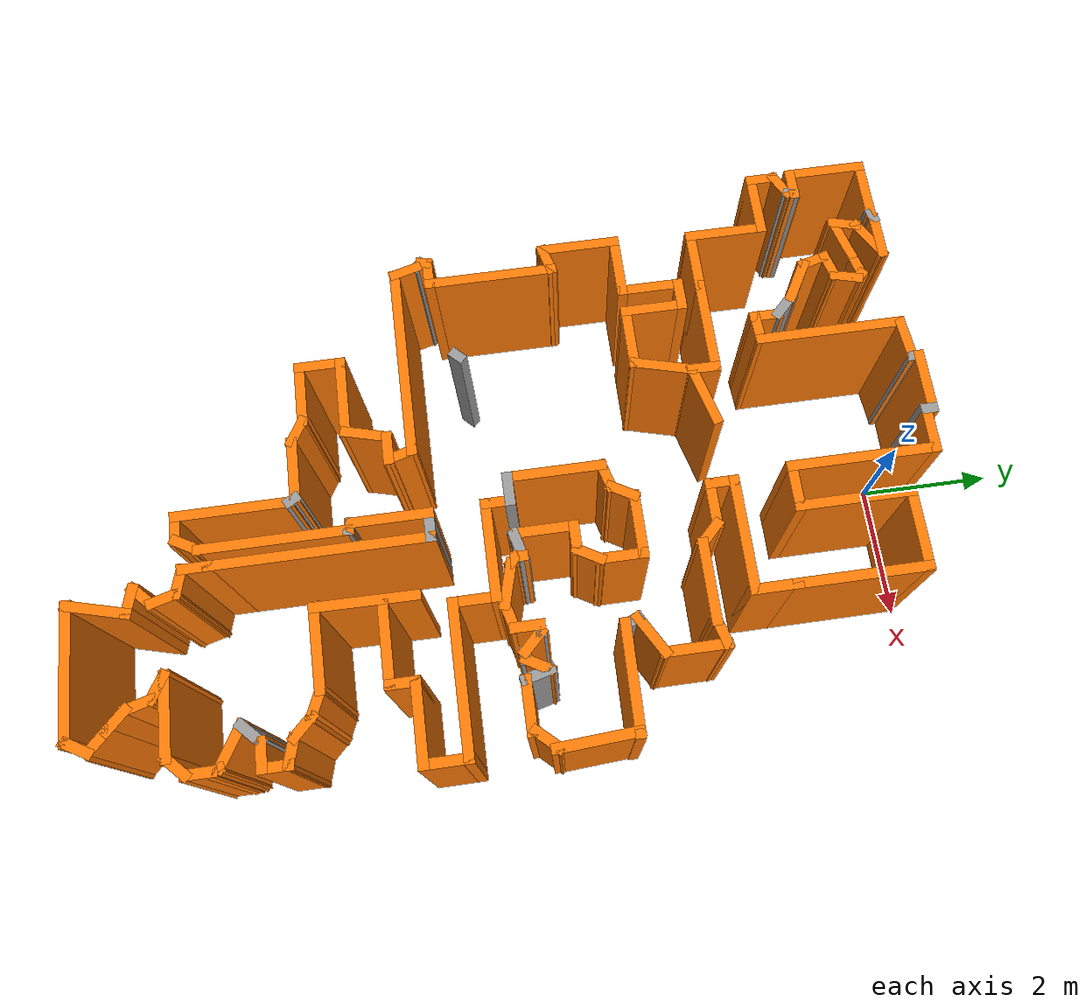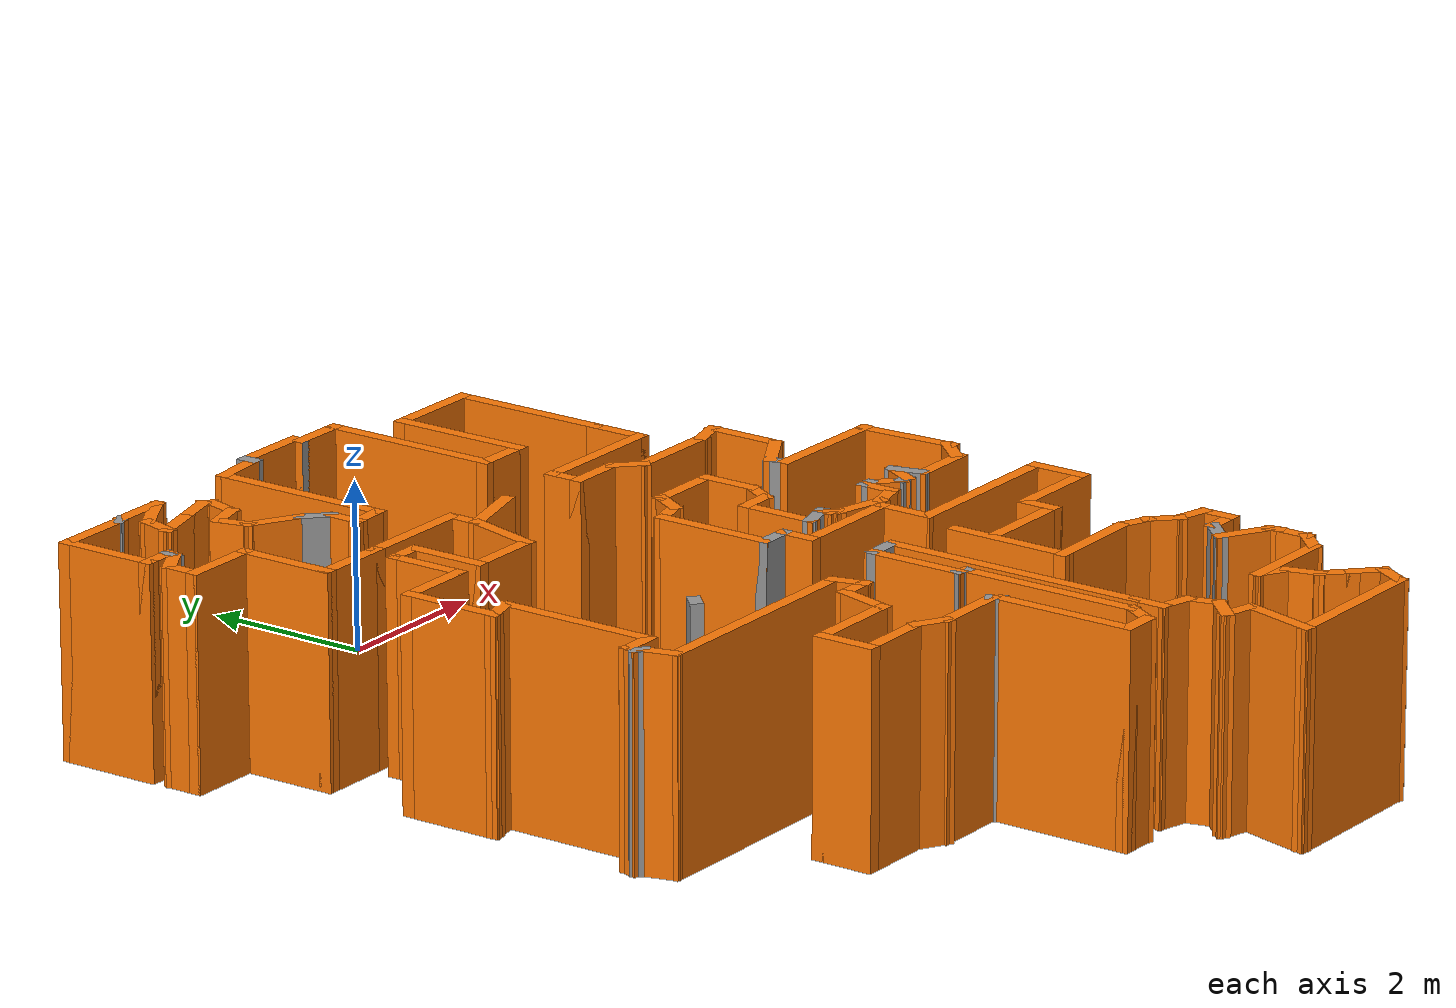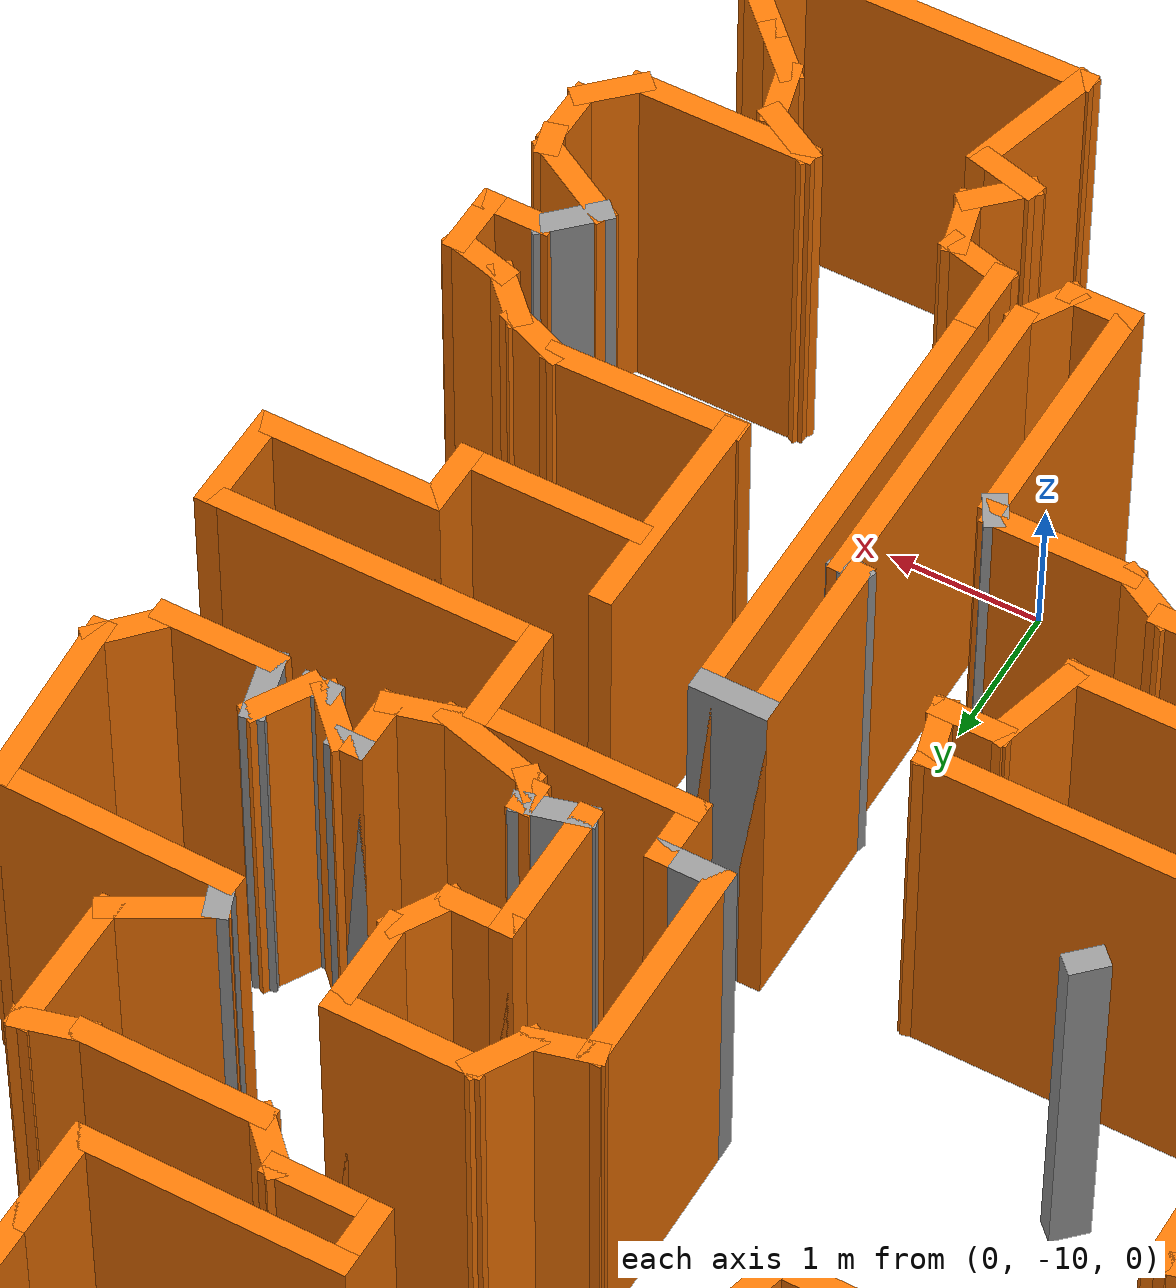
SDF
<?xml version='1.0'?>
<sdf version='1.6'>
  <model name='map_4'>
    <pose frame=''>-0.448381 -5.69762 0 0 -0 0</pose>
    <link name='Wall_0'>
      <collision name='Wall_0_Collision'>
        <geometry>
          <box>
            <size>2.25 0.15 2.5</size>
          </box>
        </geometry>
        <pose frame=''>0 0 1.25 0 -0 0</pose>
      </collision>
      <visual name='Wall_0_Visual'>
        <pose frame=''>0 0 1.25 0 -0 0</pose>
        <geometry>
          <box>
            <size>2.25 0.15 2.5</size>
          </box>
        </geometry>
        <material>
          <script>
            <uri>file://media/materials/scripts/gazebo.material</uri>
            <name>Gazebo/Grey</name>
          </script>
          <ambient>0.996078 0.47451 0.0196078 1</ambient>
        </material>
        <meta>
          <layer>0</layer>
        </meta>
      </visual>
      <pose frame=''>-1.38482 5.02012 0 0 -0 -1.5708</pose>
    </link>
    <link name='Wall_1'>
      <collision name='Wall_1_Collision'>
        <geometry>
          <box>
            <size>0.523847 0.15 2.5</size>
          </box>
        </geometry>
        <pose frame=''>0 0 1.25 0 -0 0</pose>
      </collision>
      <visual name='Wall_1_Visual'>
        <pose frame=''>0 0 1.25 0 -0 0</pose>
        <geometry>
          <box>
            <size>0.523847 0.15 2.5</size>
          </box>
        </geometry>
        <material>
          <script>
            <uri>file://media/materials/scripts/gazebo.material</uri>
            <name>Gazebo/Grey</name>
          </script>
          <ambient>0.996078 0.47451 0.0196078 1</ambient>
        </material>
        <meta>
          <layer>0</layer>
        </meta>
      </visual>
      <pose frame=''>-1.57139 3.95855 0 0 -0 -3.07968</pose>
    </link>
    <link name='Wall_100'>
      <collision name='Wall_100_Collision'>
        <geometry>
          <box>
            <size>0.5 0.15 2.5</size>
          </box>
        </geometry>
        <pose frame=''>0 0 1.25 0 -0 0</pose>
      </collision>
      <visual name='Wall_100_Visual'>
        <pose frame=''>0 0 1.25 0 -0 0</pose>
        <geometry>
          <box>
            <size>0.5 0.15 2.5</size>
          </box>
        </geometry>
        <material>
          <script>
            <uri>file://media/materials/scripts/gazebo.material</uri>
            <name>Gazebo/Grey</name>
          </script>
          <ambient>0.996078 0.47451 0.0196078 1</ambient>
        </material>
        <meta>
          <layer>0</layer>
        </meta>
      </visual>
      <pose frame=''>3.63966 -3.64447 0 0 -0 0</pose>
    </link>
    <link name='Wall_101'>
      <collision name='Wall_101_Collision'>
        <geometry>
          <box>
            <size>0.5 0.15 2.5</size>
          </box>
        </geometry>
        <pose frame=''>0 0 1.25 0 -0 0</pose>
      </collision>
      <visual name='Wall_101_Visual'>
        <pose frame=''>0 0 1.25 0 -0 0</pose>
        <geometry>
          <box>
            <size>0.5 0.15 2.5</size>
          </box>
        </geometry>
        <material>
          <script>
            <uri>file://media/materials/scripts/gazebo.material</uri>
            <name>Gazebo/Grey</name>
          </script>
          <ambient>0.996078 0.47451 0.0196078 1</ambient>
        </material>
        <meta>
          <layer>0</layer>
        </meta>
      </visual>
      <pose frame=''>3.81466 -3.46947 0 0 -0 1.5708</pose>
    </link>
    <link name='Wall_102'>
      <collision name='Wall_102_Collision'>
        <geometry>
          <box>
            <size>0.5 0.15 2.5</size>
          </box>
        </geometry>
        <pose frame=''>0 0 1.25 0 -0 0</pose>
      </collision>
      <visual name='Wall_102_Visual'>
        <pose frame=''>0 0 1.25 0 -0 0</pose>
        <geometry>
          <box>
            <size>0.5 0.15 2.5</size>
          </box>
        </geometry>
        <material>
          <script>
            <uri>file://media/materials/scripts/gazebo.material</uri>
            <name>Gazebo/Grey</name>
          </script>
          <ambient>0.996078 0.47451 0.0196078 1</ambient>
        </material>
        <meta>
          <layer>0</layer>
        </meta>
      </visual>
      <pose frame=''>3.64562 -3.24918 0 0 -0 2.87979</pose>
    </link>
    <link name='Wall_103'>
      <collision name='Wall_103_Collision'>
        <geometry>
          <box>
            <size>0.5 0.15 2.5</size>
          </box>
        </geometry>
        <pose frame=''>0 0 1.25 0 -0 0</pose>
      </collision>
      <visual name='Wall_103_Visual'>
        <pose frame=''>0 0 1.25 0 -0 0</pose>
        <geometry>
          <box>
            <size>0.5 0.15 2.5</size>
          </box>
        </geometry>
        <material>
          <script>
            <uri>file://media/materials/scripts/gazebo.material</uri>
            <name>Gazebo/Grey</name>
          </script>
          <ambient>0.996078 0.47451 0.0196078 1</ambient>
        </material>
        <meta>
          <layer>0</layer>
        </meta>
      </visual>
      <pose frame=''>3.35284 -3.08014 0 0 -0 2.35619</pose>
    </link>
    <link name='Wall_104'>
      <collision name='Wall_104_Collision'>
        <geometry>
          <box>
            <size>0.493604 0.15 2.5</size>
          </box>
        </geometry>
        <pose frame=''>0 0 1.25 0 -0 0</pose>
      </collision>
      <visual name='Wall_104_Visual'>
        <pose frame=''>0 0 1.25 0 -0 0</pose>
        <geometry>
          <box>
            <size>0.493604 0.15 2.5</size>
          </box>
        </geometry>
        <material>
          <script>
            <uri>file://media/materials/scripts/gazebo.material</uri>
            <name>Gazebo/Grey</name>
          </script>
          <ambient>0.996078 0.47451 0.0196078 1</ambient>
        </material>
        <meta>
          <layer>0</layer>
        </meta>
      </visual>
      <pose frame=''>3.06994 -2.89171 0 0 -0 2.75556</pose>
    </link>
    <link name='Wall_105'>
      <collision name='Wall_105_Collision'>
        <geometry>
          <box>
            <size>1.29573 0.15 2.5</size>
          </box>
        </geometry>
        <pose frame=''>0 0 1.25 0 -0 0</pose>
      </collision>
      <visual name='Wall_105_Visual'>
        <pose frame=''>0 0 1.25 0 -0 0</pose>
        <geometry>
          <box>
            <size>1.29573 0.15 2.5</size>
          </box>
        </geometry>
        <material>
          <script>
            <uri>file://media/materials/scripts/gazebo.material</uri>
            <name>Gazebo/Grey</name>
          </script>
          <ambient>0.996078 0.47451 0.0196078 1</ambient>
        </material>
        <meta>
          <layer>0</layer>
        </meta>
      </visual>
      <pose frame=''>2.32276 -2.83463 0 0 -0 -3.12832</pose>
    </link>
    <link name='Wall_106'>
      <collision name='Wall_106_Collision'>
        <geometry>
          <box>
            <size>1.54571 0.15 2.5</size>
          </box>
        </geometry>
        <pose frame=''>0 0 1.25 0 -0 0</pose>
      </collision>
      <visual name='Wall_106_Visual'>
        <pose frame=''>0 0 1.25 0 -0 0</pose>
        <geometry>
          <box>
            <size>1.54571 0.15 2.5</size>
          </box>
        </geometry>
        <material>
          <script>
            <uri>file://media/materials/scripts/gazebo.material</uri>
            <name>Gazebo/Grey</name>
          </script>
          <ambient>0.996078 0.47451 0.0196078 1</ambient>
        </material>
        <meta>
          <layer>0</layer>
        </meta>
      </visual>
      <pose frame=''>1.77276 -2.14442 0 0 -0 1.5599</pose>
    </link>
    <link name='Wall_108'>
      <collision name='Wall_108_Collision'>
        <geometry>
          <box>
            <size>1.25 0.15 2.5</size>
          </box>
        </geometry>
        <pose frame=''>0 0 1.25 0 -0 0</pose>
      </collision>
      <visual name='Wall_108_Visual'>
        <pose frame=''>0 0 1.25 0 -0 0</pose>
        <geometry>
          <box>
            <size>1.25 0.15 2.5</size>
          </box>
        </geometry>
        <material>
          <script>
            <uri>file://media/materials/scripts/gazebo.material</uri>
            <name>Gazebo/Grey</name>
          </script>
          <ambient>0.996078 0.47451 0.0196078 1</ambient>
        </material>
        <meta>
          <layer>0</layer>
        </meta>
      </visual>
      <pose frame=''>2.40475 -1.90642 0 0 -0 0</pose>
    </link>
    <link name='Wall_109'>
      <collision name='Wall_109_Collision'>
        <geometry>
          <box>
            <size>0.5 0.15 2.5</size>
          </box>
        </geometry>
        <pose frame=''>0 0 1.25 0 -0 0</pose>
      </collision>
      <visual name='Wall_109_Visual'>
        <pose frame=''>0 0 1.25 0 -0 0</pose>
        <geometry>
          <box>
            <size>0.5 0.15 2.5</size>
          </box>
        </geometry>
        <material>
          <script>
            <uri>file://media/materials/scripts/gazebo.material</uri>
            <name>Gazebo/Grey</name>
          </script>
          <ambient>0.996078 0.47451 0.0196078 1</ambient>
        </material>
        <meta>
          <layer>0</layer>
        </meta>
      </visual>
      <pose frame=''>2.95475 -1.73142 0 0 -0 1.5708</pose>
    </link>
    <link name='Wall_110'>
      <collision name='Wall_110_Collision'>
        <geometry>
          <box>
            <size>1.25 0.15 2.5</size>
          </box>
        </geometry>
        <pose frame=''>0 0 1.25 0 -0 0</pose>
      </collision>
      <visual name='Wall_110_Visual'>
        <pose frame=''>0 0 1.25 0 -0 0</pose>
        <geometry>
          <box>
            <size>1.25 0.15 2.5</size>
          </box>
        </geometry>
        <material>
          <script>
            <uri>file://media/materials/scripts/gazebo.material</uri>
            <name>Gazebo/Grey</name>
          </script>
          <ambient>0.996078 0.47451 0.0196078 1</ambient>
        </material>
        <meta>
          <layer>0</layer>
        </meta>
      </visual>
      <pose frame=''>3.50475 -1.55642 0 0 -0 0</pose>
    </link>
    <link name='Wall_111'>
      <collision name='Wall_111_Collision'>
        <geometry>
          <box>
            <size>0.75 0.15 2.5</size>
          </box>
        </geometry>
        <pose frame=''>0 0 1.25 0 -0 0</pose>
      </collision>
      <visual name='Wall_111_Visual'>
        <pose frame=''>0 0 1.25 0 -0 0</pose>
        <geometry>
          <box>
            <size>0.75 0.15 2.5</size>
          </box>
        </geometry>
        <material>
          <script>
            <uri>file://media/materials/scripts/gazebo.material</uri>
            <name>Gazebo/Grey</name>
          </script>
          <ambient>0.996078 0.47451 0.0196078 1</ambient>
        </material>
        <meta>
          <layer>0</layer>
        </meta>
      </visual>
      <pose frame=''>4.05475 -1.25642 0 0 -0 1.5708</pose>
    </link>
    <link name='Wall_112'>
      <collision name='Wall_112_Collision'>
        <geometry>
          <box>
            <size>2.25 0.15 2.5</size>
          </box>
        </geometry>
        <pose frame=''>0 0 1.25 0 -0 0</pose>
      </collision>
      <visual name='Wall_112_Visual'>
        <pose frame=''>0 0 1.25 0 -0 0</pose>
        <geometry>
          <box>
            <size>2.25 0.15 2.5</size>
          </box>
        </geometry>
        <material>
          <script>
            <uri>file://media/materials/scripts/gazebo.material</uri>
            <name>Gazebo/Grey</name>
          </script>
          <ambient>0.996078 0.47451 0.0196078 1</ambient>
        </material>
        <meta>
          <layer>0</layer>
        </meta>
      </visual>
      <pose frame=''>3.00475 -0.956422 0 0 -0 3.14159</pose>
    </link>
    <link name='Wall_114'>
      <collision name='Wall_114_Collision'>
        <geometry>
          <box>
            <size>0.75 0.15 2.5</size>
          </box>
        </geometry>
        <pose frame=''>0 0 1.25 0 -0 0</pose>
      </collision>
      <visual name='Wall_114_Visual'>
        <pose frame=''>0 0 1.25 0 -0 0</pose>
        <geometry>
          <box>
            <size>0.75 0.15 2.5</size>
          </box>
        </geometry>
        <material>
          <script>
            <uri>file://media/materials/scripts/gazebo.material</uri>
            <name>Gazebo/Grey</name>
          </script>
          <ambient>0.996078 0.47451 0.0196078 1</ambient>
        </material>
        <meta>
          <layer>0</layer>
        </meta>
      </visual>
      <pose frame=''>1.95475 -0.656423 0 0 -0 1.5708</pose>
    </link>
    <link name='Wall_115'>
      <collision name='Wall_115_Collision'>
        <geometry>
          <box>
            <size>1.5 0.15 2.5</size>
          </box>
        </geometry>
        <pose frame=''>0 0 1.25 0 -0 0</pose>
      </collision>
      <visual name='Wall_115_Visual'>
        <pose frame=''>0 0 1.25 0 -0 0</pose>
        <geometry>
          <box>
            <size>1.5 0.15 2.5</size>
          </box>
        </geometry>
        <material>
          <script>
            <uri>file://media/materials/scripts/gazebo.material</uri>
            <name>Gazebo/Grey</name>
          </script>
          <ambient>0.996078 0.47451 0.0196078 1</ambient>
        </material>
        <meta>
          <layer>0</layer>
        </meta>
      </visual>
      <pose frame=''>1.27975 -0.356422 0 0 -0 3.14159</pose>
    </link>
    <link name='Wall_116'>
      <collision name='Wall_116_Collision'>
        <geometry>
          <box>
            <size>0.5 0.15 2.5</size>
          </box>
        </geometry>
        <pose frame=''>0 0 1.25 0 -0 0</pose>
      </collision>
      <visual name='Wall_116_Visual'>
        <pose frame=''>0 0 1.25 0 -0 0</pose>
        <geometry>
          <box>
            <size>0.5 0.15 2.5</size>
          </box>
        </geometry>
        <material>
          <script>
            <uri>file://media/materials/scripts/gazebo.material</uri>
            <name>Gazebo/Grey</name>
          </script>
          <ambient>0.996078 0.47451 0.0196078 1</ambient>
        </material>
        <meta>
          <layer>0</layer>
        </meta>
      </visual>
      <pose frame=''>0.604748 -0.181422 0 0 -0 1.5708</pose>
    </link>
    <link name='Wall_117'>
      <collision name='Wall_117_Collision'>
        <geometry>
          <box>
            <size>0.5 0.15 2.5</size>
          </box>
        </geometry>
        <pose frame=''>0 0 1.25 0 -0 0</pose>
      </collision>
      <visual name='Wall_117_Visual'>
        <pose frame=''>0 0 1.25 0 -0 0</pose>
        <geometry>
          <box>
            <size>0.5 0.15 2.5</size>
          </box>
        </geometry>
        <material>
          <script>
            <uri>file://media/materials/scripts/gazebo.material</uri>
            <name>Gazebo/Grey</name>
          </script>
          <ambient>1 1 1 1</ambient>
        </material>
        <meta>
          <layer>0</layer>
        </meta>
      </visual>
      <pose frame=''>0.429748 -0.006423 0 0 -0 3.14159</pose>
    </link>
    <link name='Wall_118'>
      <collision name='Wall_118_Collision'>
        <geometry>
          <box>
            <size>1.5 0.15 2.5</size>
          </box>
        </geometry>
        <pose frame=''>0 0 1.25 0 -0 0</pose>
      </collision>
      <visual name='Wall_118_Visual'>
        <pose frame=''>0 0 1.25 0 -0 0</pose>
        <geometry>
          <box>
            <size>1.5 0.15 2.5</size>
          </box>
        </geometry>
        <material>
          <script>
            <uri>file://media/materials/scripts/gazebo.material</uri>
            <name>Gazebo/Grey</name>
          </script>
          <ambient>0.996078 0.47451 0.0196078 1</ambient>
        </material>
        <meta>
          <layer>0</layer>
        </meta>
      </visual>
      <pose frame=''>0.254748 0.668578 0 0 -0 1.5708</pose>
    </link>
    <link name='Wall_119'>
      <collision name='Wall_119_Collision'>
        <geometry>
          <box>
            <size>0.5 0.15 2.5</size>
          </box>
        </geometry>
        <pose frame=''>0 0 1.25 0 -0 0</pose>
      </collision>
      <visual name='Wall_119_Visual'>
        <pose frame=''>0 0 1.25 0 -0 0</pose>
        <geometry>
          <box>
            <size>0.5 0.15 2.5</size>
          </box>
        </geometry>
        <material>
          <script>
            <uri>file://media/materials/scripts/gazebo.material</uri>
            <name>Gazebo/Grey</name>
          </script>
          <ambient>0.996078 0.47451 0.0196078 1</ambient>
        </material>
        <meta>
          <layer>0</layer>
        </meta>
      </visual>
      <pose frame=''>0.423785 1.38887 0 0 -0 0.261799</pose>
    </link>
    <link name='Wall_12'>
      <collision name='Wall_12_Collision'>
        <geometry>
          <box>
            <size>0.75 0.15 2.5</size>
          </box>
        </geometry>
        <pose frame=''>0 0 1.25 0 -0 0</pose>
      </collision>
      <visual name='Wall_12_Visual'>
        <pose frame=''>0 0 1.25 0 -0 0</pose>
        <geometry>
          <box>
            <size>0.75 0.15 2.5</size>
          </box>
        </geometry>
        <material>
          <script>
            <uri>file://media/materials/scripts/gazebo.material</uri>
            <name>Gazebo/Grey</name>
          </script>
          <ambient>0.996078 0.47451 0.0196078 1</ambient>
        </material>
        <meta>
          <layer>0</layer>
        </meta>
      </visual>
      <pose frame=''>-2.88554 5.51369 0 0 -0 -2.87979</pose>
    </link>
    <link name='Wall_120'>
      <collision name='Wall_120_Collision'>
        <geometry>
          <box>
            <size>0.5 0.15 2.5</size>
          </box>
        </geometry>
        <pose frame=''>0 0 1.25 0 -0 0</pose>
      </collision>
      <visual name='Wall_120_Visual'>
        <pose frame=''>0 0 1.25 0 -0 0</pose>
        <geometry>
          <box>
            <size>0.5 0.15 2.5</size>
          </box>
        </geometry>
        <material>
          <script>
            <uri>file://media/materials/scripts/gazebo.material</uri>
            <name>Gazebo/Grey</name>
          </script>
          <ambient>0.996078 0.47451 0.0196078 1</ambient>
        </material>
        <meta>
          <layer>0</layer>
        </meta>
      </visual>
      <pose frame=''>0.680322 1.58572 0 0 -0 1.0472</pose>
    </link>
    <link name='Wall_121'>
      <collision name='Wall_121_Collision'>
        <geometry>
          <box>
            <size>1 0.15 2.5</size>
          </box>
        </geometry>
        <pose frame=''>0 0 1.25 0 -0 0</pose>
      </collision>
      <visual name='Wall_121_Visual'>
        <pose frame=''>0 0 1.25 0 -0 0</pose>
        <geometry>
          <box>
            <size>1 0.15 2.5</size>
          </box>
        </geometry>
        <material>
          <script>
            <uri>file://media/materials/scripts/gazebo.material</uri>
            <name>Gazebo/Grey</name>
          </script>
          <ambient>0.996078 0.47451 0.0196078 1</ambient>
        </material>
        <meta>
          <layer>0</layer>
        </meta>
      </visual>
      <pose frame=''>1.19282 1.73727 0 0 -0 0</pose>
    </link>
    <link name='Wall_122'>
      <collision name='Wall_122_Collision'>
        <geometry>
          <box>
            <size>0.75 0.15 2.5</size>
          </box>
        </geometry>
        <pose frame=''>0 0 1.25 0 -0 0</pose>
      </collision>
      <visual name='Wall_122_Visual'>
        <pose frame=''>0 0 1.25 0 -0 0</pose>
        <geometry>
          <box>
            <size>0.75 0.15 2.5</size>
          </box>
        </geometry>
        <material>
          <script>
            <uri>file://media/materials/scripts/gazebo.material</uri>
            <name>Gazebo/Grey</name>
          </script>
          <ambient>0.996078 0.47451 0.0196078 1</ambient>
        </material>
        <meta>
          <layer>0</layer>
        </meta>
      </visual>
      <pose frame=''>1.61782 1.43727 0 0 -0 -1.5708</pose>
    </link>
    <link name='Wall_123'>
      <collision name='Wall_123_Collision'>
        <geometry>
          <box>
            <size>0.5 0.15 2.5</size>
          </box>
        </geometry>
        <pose frame=''>0 0 1.25 0 -0 0</pose>
      </collision>
      <visual name='Wall_123_Visual'>
        <pose frame=''>0 0 1.25 0 -0 0</pose>
        <geometry>
          <box>
            <size>0.5 0.15 2.5</size>
          </box>
        </geometry>
        <material>
          <script>
            <uri>file://media/materials/scripts/gazebo.material</uri>
            <name>Gazebo/Grey</name>
          </script>
          <ambient>0.996078 0.47451 0.0196078 1</ambient>
        </material>
        <meta>
          <layer>0</layer>
        </meta>
      </visual>
      <pose frame=''>1.53032 0.985719 0 0 -0 -2.0944</pose>
    </link>
    <link name='Wall_124'>
      <collision name='Wall_124_Collision'>
        <geometry>
          <box>
            <size>0.5 0.15 2.5</size>
          </box>
        </geometry>
        <pose frame=''>0 0 1.25 0 -0 0</pose>
      </collision>
      <visual name='Wall_124_Visual'>
        <pose frame=''>0 0 1.25 0 -0 0</pose>
        <geometry>
          <box>
            <size>0.5 0.15 2.5</size>
          </box>
        </geometry>
        <material>
          <script>
            <uri>file://media/materials/scripts/gazebo.material</uri>
            <name>Gazebo/Grey</name>
          </script>
          <ambient>0.996078 0.47451 0.0196078 1</ambient>
        </material>
        <meta>
          <layer>0</layer>
        </meta>
      </visual>
      <pose frame=''>1.26782 0.834164 0 0 -0 3.14159</pose>
    </link>
    <link name='Wall_125'>
      <collision name='Wall_125_Collision'>
        <geometry>
          <box>
            <size>1 0.15 2.5</size>
          </box>
        </geometry>
        <pose frame=''>0 0 1.25 0 -0 0</pose>
      </collision>
      <visual name='Wall_125_Visual'>
        <pose frame=''>0 0 1.25 0 -0 0</pose>
        <geometry>
          <box>
            <size>1 0.15 2.5</size>
          </box>
        </geometry>
        <material>
          <script>
            <uri>file://media/materials/scripts/gazebo.material</uri>
            <name>Gazebo/Grey</name>
          </script>
          <ambient>0.996078 0.47451 0.0196078 1</ambient>
        </material>
        <meta>
          <layer>0</layer>
        </meta>
      </visual>
      <pose frame=''>1.09282 0.409164 0 0 -0 -1.5708</pose>
    </link>
    <link name='Wall_126'>
      <collision name='Wall_126_Collision'>
        <geometry>
          <box>
            <size>0.5 0.15 2.5</size>
          </box>
        </geometry>
        <pose frame=''>0 0 1.25 0 -0 0</pose>
      </collision>
      <visual name='Wall_126_Visual'>
        <pose frame=''>0 0 1.25 0 -0 0</pose>
        <geometry>
          <box>
            <size>0.5 0.15 2.5</size>
          </box>
        </geometry>
        <material>
          <script>
            <uri>file://media/materials/scripts/gazebo.material</uri>
            <name>Gazebo/Grey</name>
          </script>
          <ambient>1 1 1 1</ambient>
        </material>
        <meta>
          <layer>0</layer>
        </meta>
      </visual>
      <pose frame=''>1.26186 0.029458 0 0 -0 0.261799</pose>
    </link>
    <link name='Wall_129'>
      <collision name='Wall_129_Collision'>
        <geometry>
          <box>
            <size>0.25 0.15 2.5</size>
          </box>
        </geometry>
        <pose frame=''>0 0 1.25 0 -0 0</pose>
      </collision>
      <visual name='Wall_129_Visual'>
        <pose frame=''>0 0 1.25 0 -0 0</pose>
        <geometry>
          <box>
            <size>0.25 0.15 2.5</size>
          </box>
        </geometry>
        <material>
          <script>
            <uri>file://media/materials/scripts/gazebo.material</uri>
            <name>Gazebo/Grey</name>
          </script>
          <ambient>0.996078 0.47451 0.0196078 1</ambient>
        </material>
        <meta>
          <layer>0</layer>
        </meta>
      </visual>
      <pose frame=''>1.4309 0.024751 0 0 -0 -1.5708</pose>
    </link>
    <link name='Wall_13'>
      <collision name='Wall_13_Collision'>
        <geometry>
          <box>
            <size>0.5 0.15 2.5</size>
          </box>
        </geometry>
        <pose frame=''>0 0 1.25 0 -0 0</pose>
      </collision>
      <visual name='Wall_13_Visual'>
        <pose frame=''>0 0 1.25 0 -0 0</pose>
        <geometry>
          <box>
            <size>0.5 0.15 2.5</size>
          </box>
        </geometry>
        <material>
          <script>
            <uri>file://media/materials/scripts/gazebo.material</uri>
            <name>Gazebo/Grey</name>
          </script>
          <ambient>0.996078 0.47451 0.0196078 1</ambient>
        </material>
        <meta>
          <layer>0</layer>
        </meta>
      </visual>
      <pose frame=''>-3.13003 5.60508 0 0 -0 1.309</pose>
    </link>
    <link name='Wall_130'>
      <collision name='Wall_130_Collision'>
        <geometry>
          <box>
            <size>0.25 0.15 2.5</size>
          </box>
        </geometry>
        <pose frame=''>0 0 1.25 0 -0 0</pose>
      </collision>
      <visual name='Wall_130_Visual'>
        <pose frame=''>0 0 1.25 0 -0 0</pose>
        <geometry>
          <box>
            <size>0.25 0.15 2.5</size>
          </box>
        </geometry>
        <material>
          <script>
            <uri>file://media/materials/scripts/gazebo.material</uri>
            <name>Gazebo/Grey</name>
          </script>
          <ambient>0.996078 0.47451 0.0196078 1</ambient>
        </material>
        <meta>
          <layer>0</layer>
        </meta>
      </visual>
      <pose frame=''>1.46625 -0.060605 0 0 -0 -0.785398</pose>
    </link>
    <link name='Wall_131'>
      <collision name='Wall_131_Collision'>
        <geometry>
          <box>
            <size>0.75 0.15 2.5</size>
          </box>
        </geometry>
        <pose frame=''>0 0 1.25 0 -0 0</pose>
      </collision>
      <visual name='Wall_131_Visual'>
        <pose frame=''>0 0 1.25 0 -0 0</pose>
        <geometry>
          <box>
            <size>0.75 0.15 2.5</size>
          </box>
        </geometry>
        <material>
          <script>
            <uri>file://media/materials/scripts/gazebo.material</uri>
            <name>Gazebo/Grey</name>
          </script>
          <ambient>0.996078 0.47451 0.0196078 1</ambient>
        </material>
        <meta>
          <layer>0</layer>
        </meta>
      </visual>
      <pose frame=''>1.79138 -0.173606 0 0 -0 -0.261799</pose>
    </link>
    <link name='Wall_132'>
      <collision name='Wall_132_Collision'>
        <geometry>
          <box>
            <size>0.5 0.15 2.5</size>
          </box>
        </geometry>
        <pose frame=''>0 0 1.25 0 -0 0</pose>
      </collision>
      <visual name='Wall_132_Visual'>
        <pose frame=''>0 0 1.25 0 -0 0</pose>
        <geometry>
          <box>
            <size>0.5 0.15 2.5</size>
          </box>
        </geometry>
        <material>
          <script>
            <uri>file://media/materials/scripts/gazebo.material</uri>
            <name>Gazebo/Grey</name>
          </script>
          <ambient>0.996078 0.47451 0.0196078 1</ambient>
        </material>
        <meta>
          <layer>0</layer>
        </meta>
      </visual>
      <pose frame=''>2.2502 -0.205958 0 0 -0 0.261799</pose>
    </link>
    <link name='Wall_133'>
      <collision name='Wall_133_Collision'>
        <geometry>
          <box>
            <size>0.5 0.15 2.5</size>
          </box>
        </geometry>
        <pose frame=''>0 0 1.25 0 -0 0</pose>
      </collision>
      <visual name='Wall_133_Visual'>
        <pose frame=''>0 0 1.25 0 -0 0</pose>
        <geometry>
          <box>
            <size>0.5 0.15 2.5</size>
          </box>
        </geometry>
        <material>
          <script>
            <uri>file://media/materials/scripts/gazebo.material</uri>
            <name>Gazebo/Grey</name>
          </script>
          <ambient>0.996078 0.47451 0.0196078 1</ambient>
        </material>
        <meta>
          <layer>0</layer>
        </meta>
      </visual>
      <pose frame=''>2.41924 0.014336 0 0 -0 1.5708</pose>
    </link>
    <link name='Wall_134'>
      <collision name='Wall_134_Collision'>
        <geometry>
          <box>
            <size>0.25 0.15 2.5</size>
          </box>
        </geometry>
        <pose frame=''>0 0 1.25 0 -0 0</pose>
      </collision>
      <visual name='Wall_134_Visual'>
        <pose frame=''>0 0 1.25 0 -0 0</pose>
        <geometry>
          <box>
            <size>0.25 0.15 2.5</size>
          </box>
        </geometry>
        <material>
          <script>
            <uri>file://media/materials/scripts/gazebo.material</uri>
            <name>Gazebo/Grey</name>
          </script>
          <ambient>1 1 1 1</ambient>
        </material>
        <meta>
          <layer>0</layer>
        </meta>
      </visual>
      <pose frame=''>2.46924 0.189335 0 0 -0 0</pose>
    </link>
    <link name='Wall_135'>
      <collision name='Wall_135_Collision'>
        <geometry>
          <box>
            <size>0.5 0.15 2.5</size>
          </box>
        </geometry>
        <pose frame=''>0 0 1.25 0 -0 0</pose>
      </collision>
      <visual name='Wall_135_Visual'>
        <pose frame=''>0 0 1.25 0 -0 0</pose>
        <geometry>
          <box>
            <size>0.5 0.15 2.5</size>
          </box>
        </geometry>
        <material>
          <script>
            <uri>file://media/materials/scripts/gazebo.material</uri>
            <name>Gazebo/Grey</name>
          </script>
          <ambient>0.996078 0.47451 0.0196078 1</ambient>
        </material>
        <meta>
          <layer>0</layer>
        </meta>
      </visual>
      <pose frame=''>2.64298 0.065592 0 0 -0 -0.785398</pose>
    </link>
    <link name='Wall_136'>
      <collision name='Wall_136_Collision'>
        <geometry>
          <box>
            <size>0.25 0.15 2.5</size>
          </box>
        </geometry>
        <pose frame=''>0 0 1.25 0 -0 0</pose>
      </collision>
      <visual name='Wall_136_Visual'>
        <pose frame=''>0 0 1.25 0 -0 0</pose>
        <geometry>
          <box>
            <size>0.25 0.15 2.5</size>
          </box>
        </geometry>
        <material>
          <script>
            <uri>file://media/materials/scripts/gazebo.material</uri>
            <name>Gazebo/Grey</name>
          </script>
          <ambient>1 1 1 1</ambient>
        </material>
        <meta>
          <layer>0</layer>
        </meta>
      </visual>
      <pose frame=''>2.81672 -0.058152 0 0 -0 0</pose>
    </link>
    <link name='Wall_137'>
      <collision name='Wall_137_Collision'>
        <geometry>
          <box>
            <size>0.5 0.15 2.5</size>
          </box>
        </geometry>
        <pose frame=''>0 0 1.25 0 -0 0</pose>
      </collision>
      <visual name='Wall_137_Visual'>
        <pose frame=''>0 0 1.25 0 -0 0</pose>
        <geometry>
          <box>
            <size>0.5 0.15 2.5</size>
          </box>
        </geometry>
        <material>
          <script>
            <uri>file://media/materials/scripts/gazebo.material</uri>
            <name>Gazebo/Grey</name>
          </script>
          <ambient>0.996078 0.47451 0.0196078 1</ambient>
        </material>
        <meta>
          <layer>0</layer>
        </meta>
      </visual>
      <pose frame=''>2.95422 0.093402 0 0 -0 1.0472</pose>
    </link>
    <link name='Wall_138'>
      <collision name='Wall_138_Collision'>
        <geometry>
          <box>
            <size>0.5 0.15 2.5</size>
          </box>
        </geometry>
        <pose frame=''>0 0 1.25 0 -0 0</pose>
      </collision>
      <visual name='Wall_138_Visual'>
        <pose frame=''>0 0 1.25 0 -0 0</pose>
        <geometry>
          <box>
            <size>0.5 0.15 2.5</size>
          </box>
        </geometry>
        <material>
          <script>
            <uri>file://media/materials/scripts/gazebo.material</uri>
            <name>Gazebo/Grey</name>
          </script>
          <ambient>1 1 1 1</ambient>
        </material>
        <meta>
          <layer>0</layer>
        </meta>
      </visual>
      <pose frame=''>3.08702 0.07592 0 0 -0 -1.309</pose>
    </link>
    <link name='Wall_139'>
      <collision name='Wall_139_Collision'>
        <geometry>
          <box>
            <size>0.842522 0.15 2.5</size>
          </box>
        </geometry>
        <pose frame=''>0 0 1.25 0 -0 0</pose>
      </collision>
      <visual name='Wall_139_Visual'>
        <pose frame=''>0 0 1.25 0 -0 0</pose>
        <geometry>
          <box>
            <size>0.842522 0.15 2.5</size>
          </box>
        </geometry>
        <material>
          <script>
            <uri>file://media/materials/scripts/gazebo.material</uri>
            <name>Gazebo/Grey</name>
          </script>
          <ambient>0.996078 0.47451 0.0196078 1</ambient>
        </material>
        <meta>
          <layer>0</layer>
        </meta>
      </visual>
      <pose frame=''>3.47857 -0.093117 0 0 -0 0</pose>
    </link>
    <link name='Wall_14'>
      <collision name='Wall_14_Collision'>
        <geometry>
          <box>
            <size>0.75 0.15 2.5</size>
          </box>
        </geometry>
        <pose frame=''>0 0 1.25 0 -0 0</pose>
      </collision>
      <visual name='Wall_14_Visual'>
        <pose frame=''>0 0 1.25 0 -0 0</pose>
        <geometry>
          <box>
            <size>0.75 0.15 2.5</size>
          </box>
        </geometry>
        <material>
          <script>
            <uri>file://media/materials/scripts/gazebo.material</uri>
            <name>Gazebo/Grey</name>
          </script>
          <ambient>0.996078 0.47451 0.0196078 1</ambient>
        </material>
        <meta>
          <layer>0</layer>
        </meta>
      </visual>
      <pose frame=''>-2.82493 5.92412 0 0 -0 0.523599</pose>
    </link>
    <link name='Wall_140'>
      <collision name='Wall_140_Collision'>
        <geometry>
          <box>
            <size>0.53772 0.15 2.5</size>
          </box>
        </geometry>
        <pose frame=''>0 0 1.25 0 -0 0</pose>
      </collision>
      <visual name='Wall_140_Visual'>
        <pose frame=''>0 0 1.25 0 -0 0</pose>
        <geometry>
          <box>
            <size>0.53772 0.15 2.5</size>
          </box>
        </geometry>
        <material>
          <script>
            <uri>file://media/materials/scripts/gazebo.material</uri>
            <name>Gazebo/Grey</name>
          </script>
          <ambient>0.996078 0.47451 0.0196078 1</ambient>
        </material>
        <meta>
          <layer>0</layer>
        </meta>
      </visual>
      <pose frame=''>3.95601 0.095884 0 0 -0 0.827595</pose>
    </link>
    <link name='Wall_141'>
      <collision name='Wall_141_Collision'>
        <geometry>
          <box>
            <size>1.27527 0.15 2.5</size>
          </box>
        </geometry>
        <pose frame=''>0 0 1.25 0 -0 0</pose>
      </collision>
      <visual name='Wall_141_Visual'>
        <pose frame=''>0 0 1.25 0 -0 0</pose>
        <geometry>
          <box>
            <size>1.27527 0.15 2.5</size>
          </box>
        </geometry>
        <material>
          <script>
            <uri>file://media/materials/scripts/gazebo.material</uri>
            <name>Gazebo/Grey</name>
          </script>
          <ambient>0.996078 0.47451 0.0196078 1</ambient>
        </material>
        <meta>
          <layer>0</layer>
        </meta>
      </visual>
      <pose frame=''>4.05249 0.753929 0 0 -0 1.6325</pose>
    </link>
    <link name='Wall_142'>
      <collision name='Wall_142_Collision'>
        <geometry>
          <box>
            <size>1.63453 0.15 2.5</size>
          </box>
        </geometry>
        <pose frame=''>0 0 1.25 0 -0 0</pose>
      </collision>
      <visual name='Wall_142_Visual'>
        <pose frame=''>0 0 1.25 0 -0 0</pose>
        <geometry>
          <box>
            <size>1.63453 0.15 2.5</size>
          </box>
        </geometry>
        <material>
          <script>
            <uri>file://media/materials/scripts/gazebo.material</uri>
            <name>Gazebo/Grey</name>
          </script>
          <ambient>0.996078 0.47451 0.0196078 1</ambient>
        </material>
        <meta>
          <layer>0</layer>
        </meta>
      </visual>
      <pose frame=''>3.29875 1.32706 0 0 -0 3.12601</pose>
    </link>
    <link name='Wall_143'>
      <collision name='Wall_143_Collision'>
        <geometry>
          <box>
            <size>0.29196 0.15 2.5</size>
          </box>
        </geometry>
        <pose frame=''>0 0 1.25 0 -0 0</pose>
      </collision>
      <visual name='Wall_143_Visual'>
        <pose frame=''>0 0 1.25 0 -0 0</pose>
        <geometry>
          <box>
            <size>0.29196 0.15 2.5</size>
          </box>
        </geometry>
        <material>
          <script>
            <uri>file://media/materials/scripts/gazebo.material</uri>
            <name>Gazebo/Grey</name>
          </script>
          <ambient>1 1 1 1</ambient>
        </material>
        <meta>
          <layer>0</layer>
        </meta>
      </visual>
      <pose frame=''>2.53157 1.45132 0 0 -0 1.93073</pose>
    </link>
    <link name='Wall_144'>
      <collision name='Wall_144_Collision'>
        <geometry>
          <box>
            <size>0.75 0.15 2.5</size>
          </box>
        </geometry>
        <pose frame=''>0 0 1.25 0 -0 0</pose>
      </collision>
      <visual name='Wall_144_Visual'>
        <pose frame=''>0 0 1.25 0 -0 0</pose>
        <geometry>
          <box>
            <size>0.75 0.15 2.5</size>
          </box>
        </geometry>
        <material>
          <script>
            <uri>file://media/materials/scripts/gazebo.material</uri>
            <name>Gazebo/Grey</name>
          </script>
          <ambient>0.996078 0.47451 0.0196078 1</ambient>
        </material>
        <meta>
          <layer>0</layer>
        </meta>
      </visual>
      <pose frame=''>2.76638 1.66775 0 0 -0 0.523599</pose>
    </link>
    <link name='Wall_146'>
      <collision name='Wall_146_Collision'>
        <geometry>
          <box>
            <size>1 0.15 2.5</size>
          </box>
        </geometry>
        <pose frame=''>0 0 1.25 0 -0 0</pose>
      </collision>
      <visual name='Wall_146_Visual'>
        <pose frame=''>0 0 1.25 0 -0 0</pose>
        <geometry>
          <box>
            <size>1 0.15 2.5</size>
          </box>
        </geometry>
        <material>
          <script>
            <uri>file://media/materials/scripts/gazebo.material</uri>
            <name>Gazebo/Grey</name>
          </script>
          <ambient>0.996078 0.47451 0.0196078 1</ambient>
        </material>
        <meta>
          <layer>0</layer>
        </meta>
      </visual>
      <pose frame=''>3.02619 2.24275 0 0 -0 1.5708</pose>
    </link>
    <link name='Wall_147'>
      <collision name='Wall_147_Collision'>
        <geometry>
          <box>
            <size>0.5 0.15 2.5</size>
          </box>
        </geometry>
        <pose frame=''>0 0 1.25 0 -0 0</pose>
      </collision>
      <visual name='Wall_147_Visual'>
        <pose frame=''>0 0 1.25 0 -0 0</pose>
        <geometry>
          <box>
            <size>0.5 0.15 2.5</size>
          </box>
        </geometry>
        <material>
          <script>
            <uri>file://media/materials/scripts/gazebo.material</uri>
            <name>Gazebo/Grey</name>
          </script>
          <ambient>0.996078 0.47451 0.0196078 1</ambient>
        </material>
        <meta>
          <layer>0</layer>
        </meta>
      </visual>
      <pose frame=''>2.85715 2.62246 0 0 -0 -2.87979</pose>
    </link>
    <link name='Wall_148'>
      <collision name='Wall_148_Collision'>
        <geometry>
          <box>
            <size>1.25 0.15 2.5</size>
          </box>
        </geometry>
        <pose frame=''>0 0 1.25 0 -0 0</pose>
      </collision>
      <visual name='Wall_148_Visual'>
        <pose frame=''>0 0 1.25 0 -0 0</pose>
        <geometry>
          <box>
            <size>1.25 0.15 2.5</size>
          </box>
        </geometry>
        <material>
          <script>
            <uri>file://media/materials/scripts/gazebo.material</uri>
            <name>Gazebo/Grey</name>
          </script>
          <ambient>0.996078 0.47451 0.0196078 1</ambient>
        </material>
        <meta>
          <layer>0</layer>
        </meta>
      </visual>
      <pose frame=''>2.13811 2.57716 0 0 -0 3.14159</pose>
    </link>
    <link name='Wall_149'>
      <collision name='Wall_149_Collision'>
        <geometry>
          <box>
            <size>0.5 0.15 2.5</size>
          </box>
        </geometry>
        <pose frame=''>0 0 1.25 0 -0 0</pose>
      </collision>
      <visual name='Wall_149_Visual'>
        <pose frame=''>0 0 1.25 0 -0 0</pose>
        <geometry>
          <box>
            <size>0.5 0.15 2.5</size>
          </box>
        </geometry>
        <material>
          <script>
            <uri>file://media/materials/scripts/gazebo.material</uri>
            <name>Gazebo/Grey</name>
          </script>
          <ambient>0.996078 0.47451 0.0196078 1</ambient>
        </material>
        <meta>
          <layer>0</layer>
        </meta>
      </visual>
      <pose frame=''>1.46437 2.70091 0 0 -0 2.35619</pose>
    </link>
    <link name='Wall_15'>
      <collision name='Wall_15_Collision'>
        <geometry>
          <box>
            <size>0.75 0.15 2.5</size>
          </box>
        </geometry>
        <pose frame=''>0 0 1.25 0 -0 0</pose>
      </collision>
      <visual name='Wall_15_Visual'>
        <pose frame=''>0 0 1.25 0 -0 0</pose>
        <geometry>
          <box>
            <size>0.75 0.15 2.5</size>
          </box>
        </geometry>
        <material>
          <script>
            <uri>file://media/materials/scripts/gazebo.material</uri>
            <name>Gazebo/Grey</name>
          </script>
          <ambient>0.996078 0.47451 0.0196078 1</ambient>
        </material>
        <meta>
          <layer>0</layer>
        </meta>
      </visual>
      <pose frame=''>-2.86512 6.07412 0 0 -0 3.14159</pose>
    </link>
    <link name='Wall_150'>
      <collision name='Wall_150_Collision'>
        <geometry>
          <box>
            <size>0.75 0.15 2.5</size>
          </box>
        </geometry>
        <pose frame=''>0 0 1.25 0 -0 0</pose>
      </collision>
      <visual name='Wall_150_Visual'>
        <pose frame=''>0 0 1.25 0 -0 0</pose>
        <geometry>
          <box>
            <size>0.75 0.15 2.5</size>
          </box>
        </geometry>
        <material>
          <script>
            <uri>file://media/materials/scripts/gazebo.material</uri>
            <name>Gazebo/Grey</name>
          </script>
          <ambient>0.996078 0.47451 0.0196078 1</ambient>
        </material>
        <meta>
          <layer>0</layer>
        </meta>
      </visual>
      <pose frame=''>1.04063 2.82465 0 0 -0 3.14159</pose>
    </link>
    <link name='Wall_151'>
      <collision name='Wall_151_Collision'>
        <geometry>
          <box>
            <size>0.5 0.15 2.5</size>
          </box>
        </geometry>
        <pose frame=''>0 0 1.25 0 -0 0</pose>
      </collision>
      <visual name='Wall_151_Visual'>
        <pose frame=''>0 0 1.25 0 -0 0</pose>
        <geometry>
          <box>
            <size>0.5 0.15 2.5</size>
          </box>
        </geometry>
        <material>
          <script>
            <uri>file://media/materials/scripts/gazebo.material</uri>
            <name>Gazebo/Grey</name>
          </script>
          <ambient>0.996078 0.47451 0.0196078 1</ambient>
        </material>
        <meta>
          <layer>0</layer>
        </meta>
      </visual>
      <pose frame=''>0.740628 2.99965 0 0 -0 1.5708</pose>
    </link>
    <link name='Wall_152'>
      <collision name='Wall_152_Collision'>
        <geometry>
          <box>
            <size>1.75 0.15 2.5</size>
          </box>
        </geometry>
        <pose frame=''>0 0 1.25 0 -0 0</pose>
      </collision>
      <visual name='Wall_152_Visual'>
        <pose frame=''>0 0 1.25 0 -0 0</pose>
        <geometry>
          <box>
            <size>1.75 0.15 2.5</size>
          </box>
        </geometry>
        <material>
          <script>
            <uri>file://media/materials/scripts/gazebo.material</uri>
            <name>Gazebo/Grey</name>
          </script>
          <ambient>0.996078 0.47451 0.0196078 1</ambient>
        </material>
        <meta>
          <layer>0</layer>
        </meta>
      </visual>
      <pose frame=''>1.54063 3.17465 0 0 -0 0</pose>
    </link>
    <link name='Wall_153'>
      <collision name='Wall_153_Collision'>
        <geometry>
          <box>
            <size>0.75 0.15 2.5</size>
          </box>
        </geometry>
        <pose frame=''>0 0 1.25 0 -0 0</pose>
      </collision>
      <visual name='Wall_153_Visual'>
        <pose frame=''>0 0 1.25 0 -0 0</pose>
        <geometry>
          <box>
            <size>0.75 0.15 2.5</size>
          </box>
        </geometry>
        <material>
          <script>
            <uri>file://media/materials/scripts/gazebo.material</uri>
            <name>Gazebo/Grey</name>
          </script>
          <ambient>0.996078 0.47451 0.0196078 1</ambient>
        </material>
        <meta>
          <layer>0</layer>
        </meta>
      </visual>
      <pose frame=''>2.34063 3.47465 0 0 -0 1.5708</pose>
    </link>
    <link name='Wall_154'>
      <collision name='Wall_154_Collision'>
        <geometry>
          <box>
            <size>2 0.15 2.5</size>
          </box>
        </geometry>
        <pose frame=''>0 0 1.25 0 -0 0</pose>
      </collision>
      <visual name='Wall_154_Visual'>
        <pose frame=''>0 0 1.25 0 -0 0</pose>
        <geometry>
          <box>
            <size>2 0.15 2.5</size>
          </box>
        </geometry>
        <material>
          <script>
            <uri>file://media/materials/scripts/gazebo.material</uri>
            <name>Gazebo/Grey</name>
          </script>
          <ambient>0.996078 0.47451 0.0196078 1</ambient>
        </material>
        <meta>
          <layer>0</layer>
        </meta>
      </visual>
      <pose frame=''>2.34063 4.69965 0 0 -0 1.5708</pose>
    </link>
    <link name='Wall_159'>
      <collision name='Wall_159_Collision'>
        <geometry>
          <box>
            <size>1.25 0.15 2.5</size>
          </box>
        </geometry>
        <pose frame=''>0 0 1.25 0 -0 0</pose>
      </collision>
      <visual name='Wall_159_Visual'>
        <pose frame=''>0 0 1.25 0 -0 0</pose>
        <geometry>
          <box>
            <size>1.25 0.15 2.5</size>
          </box>
        </geometry>
        <material>
          <script>
            <uri>file://media/materials/scripts/gazebo.material</uri>
            <name>Gazebo/Grey</name>
          </script>
          <ambient>0.996078 0.47451 0.0196078 1</ambient>
        </material>
        <meta>
          <layer>0</layer>
        </meta>
      </visual>
      <pose frame=''>1.79063 5.62465 0 0 -0 3.14159</pose>
    </link>
    <link name='Wall_16'>
      <collision name='Wall_16_Collision'>
        <geometry>
          <box>
            <size>0.25 0.15 2.5</size>
          </box>
        </geometry>
        <pose frame=''>0 0 1.25 0 -0 0</pose>
      </collision>
      <visual name='Wall_16_Visual'>
        <pose frame=''>0 0 1.25 0 -0 0</pose>
        <geometry>
          <box>
            <size>0.25 0.15 2.5</size>
          </box>
        </geometry>
        <material>
          <script>
            <uri>file://media/materials/scripts/gazebo.material</uri>
            <name>Gazebo/Grey</name>
          </script>
          <ambient>1 1 1 1</ambient>
        </material>
        <meta>
          <layer>0</layer>
        </meta>
      </visual>
      <pose frame=''>-3.21341 6.06118 0 0 -0 -2.87979</pose>
    </link>
    <link name='Wall_160'>
      <collision name='Wall_160_Collision'>
        <geometry>
          <box>
            <size>1.75 0.15 2.5</size>
          </box>
        </geometry>
        <pose frame=''>0 0 1.25 0 -0 0</pose>
      </collision>
      <visual name='Wall_160_Visual'>
        <pose frame=''>0 0 1.25 0 -0 0</pose>
        <geometry>
          <box>
            <size>1.75 0.15 2.5</size>
          </box>
        </geometry>
        <material>
          <script>
            <uri>file://media/materials/scripts/gazebo.material</uri>
            <name>Gazebo/Grey</name>
          </script>
          <ambient>0.996078 0.47451 0.0196078 1</ambient>
        </material>
        <meta>
          <layer>0</layer>
        </meta>
      </visual>
      <pose frame=''>1.24063 4.82465 0 0 -0 -1.5708</pose>
    </link>
    <link name='Wall_161'>
      <collision name='Wall_161_Collision'>
        <geometry>
          <box>
            <size>0.75 0.15 2.5</size>
          </box>
        </geometry>
        <pose frame=''>0 0 1.25 0 -0 0</pose>
      </collision>
      <visual name='Wall_161_Visual'>
        <pose frame=''>0 0 1.25 0 -0 0</pose>
        <geometry>
          <box>
            <size>0.75 0.15 2.5</size>
          </box>
        </geometry>
        <material>
          <script>
            <uri>file://media/materials/scripts/gazebo.material</uri>
            <name>Gazebo/Grey</name>
          </script>
          <ambient>0.996078 0.47451 0.0196078 1</ambient>
        </material>
        <meta>
          <layer>0</layer>
        </meta>
      </visual>
      <pose frame=''>0.940628 4.02465 0 0 -0 3.14159</pose>
    </link>
    <link name='Wall_162'>
      <collision name='Wall_162_Collision'>
        <geometry>
          <box>
            <size>2.25 0.15 2.5</size>
          </box>
        </geometry>
        <pose frame=''>0 0 1.25 0 -0 0</pose>
      </collision>
      <visual name='Wall_162_Visual'>
        <pose frame=''>0 0 1.25 0 -0 0</pose>
        <geometry>
          <box>
            <size>2.25 0.15 2.5</size>
          </box>
        </geometry>
        <material>
          <script>
            <uri>file://media/materials/scripts/gazebo.material</uri>
            <name>Gazebo/Grey</name>
          </script>
          <ambient>0.996078 0.47451 0.0196078 1</ambient>
        </material>
        <meta>
          <layer>0</layer>
        </meta>
      </visual>
      <pose frame=''>0.640628 5.07465 0 0 -0 1.5708</pose>
    </link>
    <link name='Wall_163'>
      <collision name='Wall_163_Collision'>
        <geometry>
          <box>
            <size>0.75 0.15 2.5</size>
          </box>
        </geometry>
        <pose frame=''>0 0 1.25 0 -0 0</pose>
      </collision>
      <visual name='Wall_163_Visual'>
        <pose frame=''>0 0 1.25 0 -0 0</pose>
        <geometry>
          <box>
            <size>0.75 0.15 2.5</size>
          </box>
        </geometry>
        <material>
          <script>
            <uri>file://media/materials/scripts/gazebo.material</uri>
            <name>Gazebo/Grey</name>
          </script>
          <ambient>0.996078 0.47451 0.0196078 1</ambient>
        </material>
        <meta>
          <layer>0</layer>
        </meta>
      </visual>
      <pose frame=''>0.340628 6.12465 0 0 -0 3.14159</pose>
    </link>
    <link name='Wall_164'>
      <collision name='Wall_164_Collision'>
        <geometry>
          <box>
            <size>0.25 0.15 2.5</size>
          </box>
        </geometry>
        <pose frame=''>0 0 1.25 0 -0 0</pose>
      </collision>
      <visual name='Wall_164_Visual'>
        <pose frame=''>0 0 1.25 0 -0 0</pose>
        <geometry>
          <box>
            <size>0.25 0.15 2.5</size>
          </box>
        </geometry>
        <material>
          <script>
            <uri>file://media/materials/scripts/gazebo.material</uri>
            <name>Gazebo/Grey</name>
          </script>
          <ambient>1 1 1 1</ambient>
        </material>
        <meta>
          <layer>0</layer>
        </meta>
      </visual>
      <pose frame=''>0.040628 6.17465 0 0 -0 1.5708</pose>
    </link>
    <link name='Wall_165'>
      <collision name='Wall_165_Collision'>
        <geometry>
          <box>
            <size>1 0.15 2.5</size>
          </box>
        </geometry>
        <pose frame=''>0 0 1.25 0 -0 0</pose>
      </collision>
      <visual name='Wall_165_Visual'>
        <pose frame=''>0 0 1.25 0 -0 0</pose>
        <geometry>
          <box>
            <size>1 0.15 2.5</size>
          </box>
        </geometry>
        <material>
          <script>
            <uri>file://media/materials/scripts/gazebo.material</uri>
            <name>Gazebo/Grey</name>
          </script>
          <ambient>0.996078 0.47451 0.0196078 1</ambient>
        </material>
        <meta>
          <layer>0</layer>
        </meta>
      </visual>
      <pose frame=''>-0.384372 6.22465 0 0 -0 3.14159</pose>
    </link>
    <link name='Wall_166'>
      <collision name='Wall_166_Collision'>
        <geometry>
          <box>
            <size>0.25 0.15 2.5</size>
          </box>
        </geometry>
        <pose frame=''>0 0 1.25 0 -0 0</pose>
      </collision>
      <visual name='Wall_166_Visual'>
        <pose frame=''>0 0 1.25 0 -0 0</pose>
        <geometry>
          <box>
            <size>0.25 0.15 2.5</size>
          </box>
        </geometry>
        <material>
          <script>
            <uri>file://media/materials/scripts/gazebo.material</uri>
            <name>Gazebo/Grey</name>
          </script>
          <ambient>1 1 1 1</ambient>
        </material>
        <meta>
          <layer>0</layer>
        </meta>
      </visual>
      <pose frame=''>-0.809372 6.17465 0 0 -0 -1.5708</pose>
    </link>
    <link name='Wall_167'>
      <collision name='Wall_167_Collision'>
        <geometry>
          <box>
            <size>0.728027 0.15 2.5</size>
          </box>
        </geometry>
        <pose frame=''>0 0 1.25 0 -0 0</pose>
      </collision>
      <visual name='Wall_167_Visual'>
        <pose frame=''>0 0 1.25 0 -0 0</pose>
        <geometry>
          <box>
            <size>0.728027 0.15 2.5</size>
          </box>
        </geometry>
        <material>
          <script>
            <uri>file://media/materials/scripts/gazebo.material</uri>
            <name>Gazebo/Grey</name>
          </script>
          <ambient>0.996078 0.47451 0.0196078 1</ambient>
        </material>
        <meta>
          <layer>0</layer>
        </meta>
      </visual>
      <pose frame=''>-1.0971 6.09739 0 0 -0 -3.04711</pose>
    </link>
    <link name='Wall_17'>
      <collision name='Wall_17_Collision'>
        <geometry>
          <box>
            <size>1 0.15 2.5</size>
          </box>
        </geometry>
        <pose frame=''>0 0 1.25 0 -0 0</pose>
      </collision>
      <visual name='Wall_17_Visual'>
        <pose frame=''>0 0 1.25 0 -0 0</pose>
        <geometry>
          <box>
            <size>1 0.15 2.5</size>
          </box>
        </geometry>
        <material>
          <script>
            <uri>file://media/materials/scripts/gazebo.material</uri>
            <name>Gazebo/Grey</name>
          </script>
          <ambient>0.996078 0.47451 0.0196078 1</ambient>
        </material>
        <meta>
          <layer>0</layer>
        </meta>
      </visual>
      <pose frame=''>-3.68671 6.04824 0 0 -0 3.14159</pose>
    </link>
    <link name='Wall_176'>
      <collision name='Wall_176_Collision'>
        <geometry>
          <box>
            <size>1 0.15 2.5</size>
          </box>
        </geometry>
        <pose frame=''>0 0 1.25 0 -0 0</pose>
      </collision>
      <visual name='Wall_176_Visual'>
        <pose frame=''>0 0 1.25 0 -0 0</pose>
        <geometry>
          <box>
            <size>1 0.15 2.5</size>
          </box>
        </geometry>
        <material>
          <script>
            <uri>file://media/materials/scripts/gazebo.material</uri>
            <name>Gazebo/Grey</name>
          </script>
          <ambient>0.996078 0.47451 0.0196078 1</ambient>
        </material>
        <meta>
          <layer>0</layer>
        </meta>
      </visual>
      <pose frame=''>-0.630183 2.98664 0 0 -0 0.261799</pose>
    </link>
    <link name='Wall_18'>
      <collision name='Wall_18_Collision'>
        <geometry>
          <box>
            <size>1.25 0.15 2.5</size>
          </box>
        </geometry>
        <pose frame=''>0 0 1.25 0 -0 0</pose>
      </collision>
      <visual name='Wall_18_Visual'>
        <pose frame=''>0 0 1.25 0 -0 0</pose>
        <geometry>
          <box>
            <size>1.25 0.15 2.5</size>
          </box>
        </geometry>
        <material>
          <script>
            <uri>file://media/materials/scripts/gazebo.material</uri>
            <name>Gazebo/Grey</name>
          </script>
          <ambient>0.996078 0.47451 0.0196078 1</ambient>
        </material>
        <meta>
          <layer>0</layer>
        </meta>
      </visual>
      <pose frame=''>-4.11171 5.49824 0 0 -0 -1.5708</pose>
    </link>
    <link name='Wall_182'>
      <collision name='Wall_182_Collision'>
        <geometry>
          <box>
            <size>0.25 0.15 2.5</size>
          </box>
        </geometry>
        <pose frame=''>0 0 1.25 0 -0 0</pose>
      </collision>
      <visual name='Wall_182_Visual'>
        <pose frame=''>0 0 1.25 0 -0 0</pose>
        <geometry>
          <box>
            <size>0.25 0.15 2.5</size>
          </box>
        </geometry>
        <material>
          <script>
            <uri>file://media/materials/scripts/gazebo.material</uri>
            <name>Gazebo/Grey</name>
          </script>
          <ambient>1 1 1 1</ambient>
        </material>
        <meta>
          <layer>0</layer>
        </meta>
      </visual>
      <pose frame=''>-1.73175 -0.506693 0 0 -0 -2.35619</pose>
    </link>
    <link name='Wall_19'>
      <collision name='Wall_19_Collision'>
        <geometry>
          <box>
            <size>0.5 0.15 2.5</size>
          </box>
        </geometry>
        <pose frame=''>0 0 1.25 0 -0 0</pose>
      </collision>
      <visual name='Wall_19_Visual'>
        <pose frame=''>0 0 1.25 0 -0 0</pose>
        <geometry>
          <box>
            <size>0.5 0.15 2.5</size>
          </box>
        </geometry>
        <material>
          <script>
            <uri>file://media/materials/scripts/gazebo.material</uri>
            <name>Gazebo/Grey</name>
          </script>
          <ambient>0.996078 0.47451 0.0196078 1</ambient>
        </material>
        <meta>
          <layer>0</layer>
        </meta>
      </visual>
      <pose frame=''>-3.93671 4.94824 0 0 -0 0</pose>
    </link>
    <link name='Wall_2'>
      <collision name='Wall_2_Collision'>
        <geometry>
          <box>
            <size>0.5 0.15 2.5</size>
          </box>
        </geometry>
        <pose frame=''>0 0 1.25 0 -0 0</pose>
      </collision>
      <visual name='Wall_2_Visual'>
        <pose frame=''>0 0 1.25 0 -0 0</pose>
        <geometry>
          <box>
            <size>0.5 0.15 2.5</size>
          </box>
        </geometry>
        <material>
          <script>
            <uri>file://media/materials/scripts/gazebo.material</uri>
            <name>Gazebo/Grey</name>
          </script>
          <ambient>0.996078 0.47451 0.0196078 1</ambient>
        </material>
        <meta>
          <layer>0</layer>
        </meta>
      </visual>
      <pose frame=''>-1.75795 4.12199 0 0 -0 1.5708</pose>
    </link>
    <link name='Wall_20'>
      <collision name='Wall_20_Collision'>
        <geometry>
          <box>
            <size>0.25 0.15 2.5</size>
          </box>
        </geometry>
        <pose frame=''>0 0 1.25 0 -0 0</pose>
      </collision>
      <visual name='Wall_20_Visual'>
        <pose frame=''>0 0 1.25 0 -0 0</pose>
        <geometry>
          <box>
            <size>0.25 0.15 2.5</size>
          </box>
        </geometry>
        <material>
          <script>
            <uri>file://media/materials/scripts/gazebo.material</uri>
            <name>Gazebo/Grey</name>
          </script>
          <ambient>1 1 1 1</ambient>
        </material>
        <meta>
          <layer>0</layer>
        </meta>
      </visual>
      <pose frame=''>-3.77465 4.89994 0 0 -0 -1.8326</pose>
    </link>
    <link name='Wall_21'>
      <collision name='Wall_21_Collision'>
        <geometry>
          <box>
            <size>0.5 0.15 2.5</size>
          </box>
        </geometry>
        <pose frame=''>0 0 1.25 0 -0 0</pose>
      </collision>
      <visual name='Wall_21_Visual'>
        <pose frame=''>0 0 1.25 0 -0 0</pose>
        <geometry>
          <box>
            <size>0.5 0.15 2.5</size>
          </box>
        </geometry>
        <material>
          <script>
            <uri>file://media/materials/scripts/gazebo.material</uri>
            <name>Gazebo/Grey</name>
          </script>
          <ambient>0.996078 0.47451 0.0196078 1</ambient>
        </material>
        <meta>
          <layer>0</layer>
        </meta>
      </visual>
      <pose frame=''>-3.93915 4.76414 0 0 -0 -2.61799</pose>
    </link>
    <link name='Wall_22'>
      <collision name='Wall_22_Collision'>
        <geometry>
          <box>
            <size>0.5 0.15 2.5</size>
          </box>
        </geometry>
        <pose frame=''>0 0 1.25 0 -0 0</pose>
      </collision>
      <visual name='Wall_22_Visual'>
        <pose frame=''>0 0 1.25 0 -0 0</pose>
        <geometry>
          <box>
            <size>0.5 0.15 2.5</size>
          </box>
        </geometry>
        <material>
          <script>
            <uri>file://media/materials/scripts/gazebo.material</uri>
            <name>Gazebo/Grey</name>
          </script>
          <ambient>0.996078 0.47451 0.0196078 1</ambient>
        </material>
        <meta>
          <layer>0</layer>
        </meta>
      </visual>
      <pose frame=''>-4.0907 4.50164 0 0 -0 -1.5708</pose>
    </link>
    <link name='Wall_25'>
      <collision name='Wall_25_Collision'>
        <geometry>
          <box>
            <size>1 0.15 2.5</size>
          </box>
        </geometry>
        <pose frame=''>0 0 1.25 0 -0 0</pose>
      </collision>
      <visual name='Wall_25_Visual'>
        <pose frame=''>0 0 1.25 0 -0 0</pose>
        <geometry>
          <box>
            <size>1 0.15 2.5</size>
          </box>
        </geometry>
        <material>
          <script>
            <uri>file://media/materials/scripts/gazebo.material</uri>
            <name>Gazebo/Grey</name>
          </script>
          <ambient>0.996078 0.47451 0.0196078 1</ambient>
        </material>
        <meta>
          <layer>0</layer>
        </meta>
      </visual>
      <pose frame=''>-3.6657 4.32664 0 0 -0 0</pose>
    </link>
    <link name='Wall_26'>
      <collision name='Wall_26_Collision'>
        <geometry>
          <box>
            <size>1.25 0.15 2.5</size>
          </box>
        </geometry>
        <pose frame=''>0 0 1.25 0 -0 0</pose>
      </collision>
      <visual name='Wall_26_Visual'>
        <pose frame=''>0 0 1.25 0 -0 0</pose>
        <geometry>
          <box>
            <size>1.25 0.15 2.5</size>
          </box>
        </geometry>
        <material>
          <script>
            <uri>file://media/materials/scripts/gazebo.material</uri>
            <name>Gazebo/Grey</name>
          </script>
          <ambient>0.996078 0.47451 0.0196078 1</ambient>
        </material>
        <meta>
          <layer>0</layer>
        </meta>
      </visual>
      <pose frame=''>-3.2407 3.77664 0 0 -0 -1.5708</pose>
    </link>
    <link name='Wall_3'>
      <collision name='Wall_3_Collision'>
        <geometry>
          <box>
            <size>0.5 0.15 2.5</size>
          </box>
        </geometry>
        <pose frame=''>0 0 1.25 0 -0 0</pose>
      </collision>
      <visual name='Wall_3_Visual'>
        <pose frame=''>0 0 1.25 0 -0 0</pose>
        <geometry>
          <box>
            <size>0.5 0.15 2.5</size>
          </box>
        </geometry>
        <material>
          <script>
            <uri>file://media/materials/scripts/gazebo.material</uri>
            <name>Gazebo/Grey</name>
          </script>
          <ambient>1 1 1 1</ambient>
        </material>
        <meta>
          <layer>0</layer>
        </meta>
      </visual>
      <pose frame=''>-1.88169 4.42073 0 0 -0 2.35619</pose>
    </link>
    <link name='Wall_30'>
      <collision name='Wall_30_Collision'>
        <geometry>
          <box>
            <size>1 0.15 2.5</size>
          </box>
        </geometry>
        <pose frame=''>0 0 1.25 0 -0 0</pose>
      </collision>
      <visual name='Wall_30_Visual'>
        <pose frame=''>0 0 1.25 0 -0 0</pose>
        <geometry>
          <box>
            <size>1 0.15 2.5</size>
          </box>
        </geometry>
        <material>
          <script>
            <uri>file://media/materials/scripts/gazebo.material</uri>
            <name>Gazebo/Grey</name>
          </script>
          <ambient>0.996078 0.47451 0.0196078 1</ambient>
        </material>
        <meta>
          <layer>0</layer>
        </meta>
      </visual>
      <pose frame=''>-2.8157 3.22664 0 0 -0 0</pose>
    </link>
    <link name='Wall_31'>
      <collision name='Wall_31_Collision'>
        <geometry>
          <box>
            <size>1.5 0.15 2.5</size>
          </box>
        </geometry>
        <pose frame=''>0 0 1.25 0 -0 0</pose>
      </collision>
      <visual name='Wall_31_Visual'>
        <pose frame=''>0 0 1.25 0 -0 0</pose>
        <geometry>
          <box>
            <size>1.5 0.15 2.5</size>
          </box>
        </geometry>
        <material>
          <script>
            <uri>file://media/materials/scripts/gazebo.material</uri>
            <name>Gazebo/Grey</name>
          </script>
          <ambient>0.996078 0.47451 0.0196078 1</ambient>
        </material>
        <meta>
          <layer>0</layer>
        </meta>
      </visual>
      <pose frame=''>-1.7157 3.22664 0 0 -0 0</pose>
    </link>
    <link name='Wall_32'>
      <collision name='Wall_32_Collision'>
        <geometry>
          <box>
            <size>0.5 0.15 2.5</size>
          </box>
        </geometry>
        <pose frame=''>0 0 1.25 0 -0 0</pose>
      </collision>
      <visual name='Wall_32_Visual'>
        <pose frame=''>0 0 1.25 0 -0 0</pose>
        <geometry>
          <box>
            <size>0.5 0.15 2.5</size>
          </box>
        </geometry>
        <material>
          <script>
            <uri>file://media/materials/scripts/gazebo.material</uri>
            <name>Gazebo/Grey</name>
          </script>
          <ambient>0.996078 0.47451 0.0196078 1</ambient>
        </material>
        <meta>
          <layer>0</layer>
        </meta>
      </visual>
      <pose frame=''>-1.0407 3.05164 0 0 -0 -1.5708</pose>
    </link>
    <link name='Wall_33'>
      <collision name='Wall_33_Collision'>
        <geometry>
          <box>
            <size>1 0.15 2.5</size>
          </box>
        </geometry>
        <pose frame=''>0 0 1.25 0 -0 0</pose>
      </collision>
      <visual name='Wall_33_Visual'>
        <pose frame=''>0 0 1.25 0 -0 0</pose>
        <geometry>
          <box>
            <size>1 0.15 2.5</size>
          </box>
        </geometry>
        <material>
          <script>
            <uri>file://media/materials/scripts/gazebo.material</uri>
            <name>Gazebo/Grey</name>
          </script>
          <ambient>0.996078 0.47451 0.0196078 1</ambient>
        </material>
        <meta>
          <layer>0</layer>
        </meta>
      </visual>
      <pose frame=''>-1.1507 2.46612 0 0 -0 -1.8326</pose>
    </link>
    <link name='Wall_34'>
      <collision name='Wall_34_Collision'>
        <geometry>
          <box>
            <size>1 0.15 2.5</size>
          </box>
        </geometry>
        <pose frame=''>0 0 1.25 0 -0 0</pose>
      </collision>
      <visual name='Wall_34_Visual'>
        <pose frame=''>0 0 1.25 0 -0 0</pose>
        <geometry>
          <box>
            <size>1 0.15 2.5</size>
          </box>
        </geometry>
        <material>
          <script>
            <uri>file://media/materials/scripts/gazebo.material</uri>
            <name>Gazebo/Grey</name>
          </script>
          <ambient>0.996078 0.47451 0.0196078 1</ambient>
        </material>
        <meta>
          <layer>0</layer>
        </meta>
      </visual>
      <pose frame=''>-1.6857 2.05561 0 0 -0 3.14159</pose>
    </link>
    <link name='Wall_35'>
      <collision name='Wall_35_Collision'>
        <geometry>
          <box>
            <size>1 0.15 2.5</size>
          </box>
        </geometry>
        <pose frame=''>0 0 1.25 0 -0 0</pose>
      </collision>
      <visual name='Wall_35_Visual'>
        <pose frame=''>0 0 1.25 0 -0 0</pose>
        <geometry>
          <box>
            <size>1 0.15 2.5</size>
          </box>
        </geometry>
        <material>
          <script>
            <uri>file://media/materials/scripts/gazebo.material</uri>
            <name>Gazebo/Grey</name>
          </script>
          <ambient>0.996078 0.47451 0.0196078 1</ambient>
        </material>
        <meta>
          <layer>0</layer>
        </meta>
      </visual>
      <pose frame=''>-2.1107 2.48061 0 0 -0 1.5708</pose>
    </link>
    <link name='Wall_36'>
      <collision name='Wall_36_Collision'>
        <geometry>
          <box>
            <size>0.5 0.15 2.5</size>
          </box>
        </geometry>
        <pose frame=''>0 0 1.25 0 -0 0</pose>
      </collision>
      <visual name='Wall_36_Visual'>
        <pose frame=''>0 0 1.25 0 -0 0</pose>
        <geometry>
          <box>
            <size>0.5 0.15 2.5</size>
          </box>
        </geometry>
        <material>
          <script>
            <uri>file://media/materials/scripts/gazebo.material</uri>
            <name>Gazebo/Grey</name>
          </script>
          <ambient>0.996078 0.47451 0.0196078 1</ambient>
        </material>
        <meta>
          <layer>0</layer>
        </meta>
      </visual>
      <pose frame=''>-2.2857 2.90561 0 0 -0 3.14159</pose>
    </link>
    <link name='Wall_37'>
      <collision name='Wall_37_Collision'>
        <geometry>
          <box>
            <size>1 0.15 2.5</size>
          </box>
        </geometry>
        <pose frame=''>0 0 1.25 0 -0 0</pose>
      </collision>
      <visual name='Wall_37_Visual'>
        <pose frame=''>0 0 1.25 0 -0 0</pose>
        <geometry>
          <box>
            <size>1 0.15 2.5</size>
          </box>
        </geometry>
        <material>
          <script>
            <uri>file://media/materials/scripts/gazebo.material</uri>
            <name>Gazebo/Grey</name>
          </script>
          <ambient>0.996078 0.47451 0.0196078 1</ambient>
        </material>
        <meta>
          <layer>0</layer>
        </meta>
      </visual>
      <pose frame=''>-2.4607 2.48061 0 0 -0 -1.5708</pose>
    </link>
    <link name='Wall_38'>
      <collision name='Wall_38_Collision'>
        <geometry>
          <box>
            <size>1 0.15 2.5</size>
          </box>
        </geometry>
        <pose frame=''>0 0 1.25 0 -0 0</pose>
      </collision>
      <visual name='Wall_38_Visual'>
        <pose frame=''>0 0 1.25 0 -0 0</pose>
        <geometry>
          <box>
            <size>1 0.15 2.5</size>
          </box>
        </geometry>
        <material>
          <script>
            <uri>file://media/materials/scripts/gazebo.material</uri>
            <name>Gazebo/Grey</name>
          </script>
          <ambient>0.996078 0.47451 0.0196078 1</ambient>
        </material>
        <meta>
          <layer>0</layer>
        </meta>
      </visual>
      <pose frame=''>-2.8857 2.05561 0 0 -0 3.14159</pose>
    </link>
    <link name='Wall_4'>
      <collision name='Wall_4_Collision'>
        <geometry>
          <box>
            <size>0.75 0.15 2.5</size>
          </box>
        </geometry>
        <pose frame=''>0 0 1.25 0 -0 0</pose>
      </collision>
      <visual name='Wall_4_Visual'>
        <pose frame=''>0 0 1.25 0 -0 0</pose>
        <geometry>
          <box>
            <size>0.75 0.15 2.5</size>
          </box>
        </geometry>
        <material>
          <script>
            <uri>file://media/materials/scripts/gazebo.material</uri>
            <name>Gazebo/Grey</name>
          </script>
          <ambient>0.996078 0.47451 0.0196078 1</ambient>
        </material>
        <meta>
          <layer>0</layer>
        </meta>
      </visual>
      <pose frame=''>-2.26525 4.69448 0 0 -0 2.61799</pose>
    </link>
    <link name='Wall_43'>
      <collision name='Wall_43_Collision'>
        <geometry>
          <box>
            <size>1.25 0.15 2.5</size>
          </box>
        </geometry>
        <pose frame=''>0 0 1.25 0 -0 0</pose>
      </collision>
      <visual name='Wall_43_Visual'>
        <pose frame=''>0 0 1.25 0 -0 0</pose>
        <geometry>
          <box>
            <size>1.25 0.15 2.5</size>
          </box>
        </geometry>
        <material>
          <script>
            <uri>file://media/materials/scripts/gazebo.material</uri>
            <name>Gazebo/Grey</name>
          </script>
          <ambient>0.996078 0.47451 0.0196078 1</ambient>
        </material>
        <meta>
          <layer>0</layer>
        </meta>
      </visual>
      <pose frame=''>-3.3107 1.50561 0 0 -0 -1.5708</pose>
    </link>
    <link name='Wall_44'>
      <collision name='Wall_44_Collision'>
        <geometry>
          <box>
            <size>0.5 0.15 2.5</size>
          </box>
        </geometry>
        <pose frame=''>0 0 1.25 0 -0 0</pose>
      </collision>
      <visual name='Wall_44_Visual'>
        <pose frame=''>0 0 1.25 0 -0 0</pose>
        <geometry>
          <box>
            <size>0.5 0.15 2.5</size>
          </box>
        </geometry>
        <material>
          <script>
            <uri>file://media/materials/scripts/gazebo.material</uri>
            <name>Gazebo/Grey</name>
          </script>
          <ambient>0.996078 0.47451 0.0196078 1</ambient>
        </material>
        <meta>
          <layer>0</layer>
        </meta>
      </visual>
      <pose frame=''>-3.14166 1.0009 0 0 -0 0.261799</pose>
    </link>
    <link name='Wall_46'>
      <collision name='Wall_46_Collision'>
        <geometry>
          <box>
            <size>2 0.15 2.5</size>
          </box>
        </geometry>
        <pose frame=''>0 0 1.25 0 -0 0</pose>
      </collision>
      <visual name='Wall_46_Visual'>
        <pose frame=''>0 0 1.25 0 -0 0</pose>
        <geometry>
          <box>
            <size>2 0.15 2.5</size>
          </box>
        </geometry>
        <material>
          <script>
            <uri>file://media/materials/scripts/gazebo.material</uri>
            <name>Gazebo/Grey</name>
          </script>
          <ambient>0.996078 0.47451 0.0196078 1</ambient>
        </material>
        <meta>
          <layer>0</layer>
        </meta>
      </visual>
      <pose frame=''>-2.97262 0.121192 0 0 -0 -1.5708</pose>
    </link>
    <link name='Wall_47'>
      <collision name='Wall_47_Collision'>
        <geometry>
          <box>
            <size>0.5 0.15 2.5</size>
          </box>
        </geometry>
        <pose frame=''>0 0 1.25 0 -0 0</pose>
      </collision>
      <visual name='Wall_47_Visual'>
        <pose frame=''>0 0 1.25 0 -0 0</pose>
        <geometry>
          <box>
            <size>0.5 0.15 2.5</size>
          </box>
        </geometry>
        <material>
          <script>
            <uri>file://media/materials/scripts/gazebo.material</uri>
            <name>Gazebo/Grey</name>
          </script>
          <ambient>0.996078 0.47451 0.0196078 1</ambient>
        </material>
        <meta>
          <layer>0</layer>
        </meta>
      </visual>
      <pose frame=''>-3.14762 -0.803808 0 0 -0 3.14159</pose>
    </link>
    <link name='Wall_48'>
      <collision name='Wall_48_Collision'>
        <geometry>
          <box>
            <size>0.25 0.15 2.5</size>
          </box>
        </geometry>
        <pose frame=''>0 0 1.25 0 -0 0</pose>
      </collision>
      <visual name='Wall_48_Visual'>
        <pose frame=''>0 0 1.25 0 -0 0</pose>
        <geometry>
          <box>
            <size>0.25 0.15 2.5</size>
          </box>
        </geometry>
        <material>
          <script>
            <uri>file://media/materials/scripts/gazebo.material</uri>
            <name>Gazebo/Grey</name>
          </script>
          <ambient>0.996078 0.47451 0.0196078 1</ambient>
        </material>
        <meta>
          <layer>0</layer>
        </meta>
      </visual>
      <pose frame=''>-3.33556 -0.852104 0 0 -0 -1.8326</pose>
    </link>
    <link name='Wall_49'>
      <collision name='Wall_49_Collision'>
        <geometry>
          <box>
            <size>0.25 0.15 2.5</size>
          </box>
        </geometry>
        <pose frame=''>0 0 1.25 0 -0 0</pose>
      </collision>
      <visual name='Wall_49_Visual'>
        <pose frame=''>0 0 1.25 0 -0 0</pose>
        <geometry>
          <box>
            <size>0.25 0.15 2.5</size>
          </box>
        </geometry>
        <material>
          <script>
            <uri>file://media/materials/scripts/gazebo.material</uri>
            <name>Gazebo/Grey</name>
          </script>
          <ambient>1 1 1 1</ambient>
        </material>
        <meta>
          <layer>0</layer>
        </meta>
      </visual>
      <pose frame=''>-3.31315 -0.935756 0 0 -0 -0.785398</pose>
    </link>
    <link name='Wall_5'>
      <collision name='Wall_5_Collision'>
        <geometry>
          <box>
            <size>0.5 0.15 2.5</size>
          </box>
        </geometry>
        <pose frame=''>0 0 1.25 0 -0 0</pose>
      </collision>
      <visual name='Wall_5_Visual'>
        <pose frame=''>0 0 1.25 0 -0 0</pose>
        <geometry>
          <box>
            <size>0.5 0.15 2.5</size>
          </box>
        </geometry>
        <material>
          <script>
            <uri>file://media/materials/scripts/gazebo.material</uri>
            <name>Gazebo/Grey</name>
          </script>
          <ambient>0.996078 0.47451 0.0196078 1</ambient>
        </material>
        <meta>
          <layer>0</layer>
        </meta>
      </visual>
      <pose frame=''>-2.57035 5.01351 0 0 -0 1.8326</pose>
    </link>
    <link name='Wall_50'>
      <collision name='Wall_50_Collision'>
        <geometry>
          <box>
            <size>0.5 0.15 2.5</size>
          </box>
        </geometry>
        <pose frame=''>0 0 1.25 0 -0 0</pose>
      </collision>
      <visual name='Wall_50_Visual'>
        <pose frame=''>0 0 1.25 0 -0 0</pose>
        <geometry>
          <box>
            <size>0.5 0.15 2.5</size>
          </box>
        </geometry>
        <material>
          <script>
            <uri>file://media/materials/scripts/gazebo.material</uri>
            <name>Gazebo/Grey</name>
          </script>
          <ambient>0.996078 0.47451 0.0196078 1</ambient>
        </material>
        <meta>
          <layer>0</layer>
        </meta>
      </visual>
      <pose frame=''>-3.2325 -1.14015 0 0 -0 -1.309</pose>
    </link>
    <link name='Wall_51'>
      <collision name='Wall_51_Collision'>
        <geometry>
          <box>
            <size>3 0.15 2.5</size>
          </box>
        </geometry>
        <pose frame=''>0 0 1.25 0 -0 0</pose>
      </collision>
      <visual name='Wall_51_Visual'>
        <pose frame=''>0 0 1.25 0 -0 0</pose>
        <geometry>
          <box>
            <size>3 0.15 2.5</size>
          </box>
        </geometry>
        <material>
          <script>
            <uri>file://media/materials/scripts/gazebo.material</uri>
            <name>Gazebo/Grey</name>
          </script>
          <ambient>0.996078 0.47451 0.0196078 1</ambient>
        </material>
        <meta>
          <layer>0</layer>
        </meta>
      </visual>
      <pose frame=''>-1.76221 -1.30919 0 0 -0 0</pose>
    </link>
    <link name='Wall_52'>
      <collision name='Wall_52_Collision'>
        <geometry>
          <box>
            <size>0.5 0.15 2.5</size>
          </box>
        </geometry>
        <pose frame=''>0 0 1.25 0 -0 0</pose>
      </collision>
      <visual name='Wall_52_Visual'>
        <pose frame=''>0 0 1.25 0 -0 0</pose>
        <geometry>
          <box>
            <size>0.5 0.15 2.5</size>
          </box>
        </geometry>
        <material>
          <script>
            <uri>file://media/materials/scripts/gazebo.material</uri>
            <name>Gazebo/Grey</name>
          </script>
          <ambient>0.996078 0.47451 0.0196078 1</ambient>
        </material>
        <meta>
          <layer>0</layer>
        </meta>
      </visual>
      <pose frame=''>-0.291915 -1.47822 0 0 -0 -1.309</pose>
    </link>
    <link name='Wall_53'>
      <collision name='Wall_53_Collision'>
        <geometry>
          <box>
            <size>0.5 0.15 2.5</size>
          </box>
        </geometry>
        <pose frame=''>0 0 1.25 0 -0 0</pose>
      </collision>
      <visual name='Wall_53_Visual'>
        <pose frame=''>0 0 1.25 0 -0 0</pose>
        <geometry>
          <box>
            <size>0.5 0.15 2.5</size>
          </box>
        </geometry>
        <material>
          <script>
            <uri>file://media/materials/scripts/gazebo.material</uri>
            <name>Gazebo/Grey</name>
          </script>
          <ambient>0.996078 0.47451 0.0196078 1</ambient>
        </material>
        <meta>
          <layer>0</layer>
        </meta>
      </visual>
      <pose frame=''>-0.421622 -1.64726 0 0 -0 3.14159</pose>
    </link>
    <link name='Wall_54'>
      <collision name='Wall_54_Collision'>
        <geometry>
          <box>
            <size>0.75 0.15 2.5</size>
          </box>
        </geometry>
        <pose frame=''>0 0 1.25 0 -0 0</pose>
      </collision>
      <visual name='Wall_54_Visual'>
        <pose frame=''>0 0 1.25 0 -0 0</pose>
        <geometry>
          <box>
            <size>0.75 0.15 2.5</size>
          </box>
        </geometry>
        <material>
          <script>
            <uri>file://media/materials/scripts/gazebo.material</uri>
            <name>Gazebo/Grey</name>
          </script>
          <ambient>0.996078 0.47451 0.0196078 1</ambient>
        </material>
        <meta>
          <layer>0</layer>
        </meta>
      </visual>
      <pose frame=''>-0.674268 -1.93704 0 0 -0 -1.8326</pose>
    </link>
    <link name='Wall_55'>
      <collision name='Wall_55_Collision'>
        <geometry>
          <box>
            <size>1.25 0.15 2.5</size>
          </box>
        </geometry>
        <pose frame=''>0 0 1.25 0 -0 0</pose>
      </collision>
      <visual name='Wall_55_Visual'>
        <pose frame=''>0 0 1.25 0 -0 0</pose>
        <geometry>
          <box>
            <size>1.25 0.15 2.5</size>
          </box>
        </geometry>
        <material>
          <script>
            <uri>file://media/materials/scripts/gazebo.material</uri>
            <name>Gazebo/Grey</name>
          </script>
          <ambient>0.996078 0.47451 0.0196078 1</ambient>
        </material>
        <meta>
          <layer>0</layer>
        </meta>
      </visual>
      <pose frame=''>-1.30191 -2.22681 0 0 -0 3.14159</pose>
    </link>
    <link name='Wall_6'>
      <collision name='Wall_6_Collision'>
        <geometry>
          <box>
            <size>0.5 0.15 2.5</size>
          </box>
        </geometry>
        <pose frame=''>0 0 1.25 0 -0 0</pose>
      </collision>
      <visual name='Wall_6_Visual'>
        <pose frame=''>0 0 1.25 0 -0 0</pose>
        <geometry>
          <box>
            <size>0.5 0.15 2.5</size>
          </box>
        </geometry>
        <material>
          <script>
            <uri>file://media/materials/scripts/gazebo.material</uri>
            <name>Gazebo/Grey</name>
          </script>
          <ambient>0.996078 0.47451 0.0196078 1</ambient>
        </material>
        <meta>
          <layer>0</layer>
        </meta>
      </visual>
      <pose frame=''>-2.4466 5.22784 0 0 -0 0.261799</pose>
    </link>
    <link name='Wall_60'>
      <collision name='Wall_60_Collision'>
        <geometry>
          <box>
            <size>0.75 0.15 2.5</size>
          </box>
        </geometry>
        <pose frame=''>0 0 1.25 0 -0 0</pose>
      </collision>
      <visual name='Wall_60_Visual'>
        <pose frame=''>0 0 1.25 0 -0 0</pose>
        <geometry>
          <box>
            <size>0.75 0.15 2.5</size>
          </box>
        </geometry>
        <material>
          <script>
            <uri>file://media/materials/scripts/gazebo.material</uri>
            <name>Gazebo/Grey</name>
          </script>
          <ambient>0.996078 0.47451 0.0196078 1</ambient>
        </material>
        <meta>
          <layer>0</layer>
        </meta>
      </visual>
      <pose frame=''>-1.85191 -2.52682 0 0 -0 -1.5708</pose>
    </link>
    <link name='Wall_61'>
      <collision name='Wall_61_Collision'>
        <geometry>
          <box>
            <size>1 0.15 2.5</size>
          </box>
        </geometry>
        <pose frame=''>0 0 1.25 0 -0 0</pose>
      </collision>
      <visual name='Wall_61_Visual'>
        <pose frame=''>0 0 1.25 0 -0 0</pose>
        <geometry>
          <box>
            <size>1 0.15 2.5</size>
          </box>
        </geometry>
        <material>
          <script>
            <uri>file://media/materials/scripts/gazebo.material</uri>
            <name>Gazebo/Grey</name>
          </script>
          <ambient>0.996078 0.47451 0.0196078 1</ambient>
        </material>
        <meta>
          <layer>0</layer>
        </meta>
      </visual>
      <pose frame=''>-1.42691 -2.82681 0 0 -0 0</pose>
    </link>
    <link name='Wall_62'>
      <collision name='Wall_62_Collision'>
        <geometry>
          <box>
            <size>0.5 0.15 2.5</size>
          </box>
        </geometry>
        <pose frame=''>0 0 1.25 0 -0 0</pose>
      </collision>
      <visual name='Wall_62_Visual'>
        <pose frame=''>0 0 1.25 0 -0 0</pose>
        <geometry>
          <box>
            <size>0.5 0.15 2.5</size>
          </box>
        </geometry>
        <material>
          <script>
            <uri>file://media/materials/scripts/gazebo.material</uri>
            <name>Gazebo/Grey</name>
          </script>
          <ambient>0.996078 0.47451 0.0196078 1</ambient>
        </material>
        <meta>
          <layer>0</layer>
        </meta>
      </visual>
      <pose frame=''>-0.850359 -2.91431 0 0 -0 -0.523599</pose>
    </link>
    <link name='Wall_68'>
      <collision name='Wall_68_Collision'>
        <geometry>
          <box>
            <size>1 0.15 2.5</size>
          </box>
        </geometry>
        <pose frame=''>0 0 1.25 0 -0 0</pose>
      </collision>
      <visual name='Wall_68_Visual'>
        <pose frame=''>0 0 1.25 0 -0 0</pose>
        <geometry>
          <box>
            <size>1 0.15 2.5</size>
          </box>
        </geometry>
        <material>
          <script>
            <uri>file://media/materials/scripts/gazebo.material</uri>
            <name>Gazebo/Grey</name>
          </script>
          <ambient>0.996078 0.47451 0.0196078 1</ambient>
        </material>
        <meta>
          <layer>0</layer>
        </meta>
      </visual>
      <pose frame=''>-0.273804 -3.00182 0 0 -0 0</pose>
    </link>
    <link name='Wall_69'>
      <collision name='Wall_69_Collision'>
        <geometry>
          <box>
            <size>0.25 0.15 2.5</size>
          </box>
        </geometry>
        <pose frame=''>0 0 1.25 0 -0 0</pose>
      </collision>
      <visual name='Wall_69_Visual'>
        <pose frame=''>0 0 1.25 0 -0 0</pose>
        <geometry>
          <box>
            <size>0.25 0.15 2.5</size>
          </box>
        </geometry>
        <material>
          <script>
            <uri>file://media/materials/scripts/gazebo.material</uri>
            <name>Gazebo/Grey</name>
          </script>
          <ambient>1 1 1 1</ambient>
        </material>
        <meta>
          <layer>0</layer>
        </meta>
      </visual>
      <pose frame=''>0.176196 -3.04512 0 0 -0 -1.0472</pose>
    </link>
    <link name='Wall_7'>
      <collision name='Wall_7_Collision'>
        <geometry>
          <box>
            <size>0.5 0.15 2.5</size>
          </box>
        </geometry>
        <pose frame=''>0 0 1.25 0 -0 0</pose>
      </collision>
      <visual name='Wall_7_Visual'>
        <pose frame=''>0 0 1.25 0 -0 0</pose>
        <geometry>
          <box>
            <size>0.5 0.15 2.5</size>
          </box>
        </geometry>
        <material>
          <script>
            <uri>file://media/materials/scripts/gazebo.material</uri>
            <name>Gazebo/Grey</name>
          </script>
          <ambient>0.996078 0.47451 0.0196078 1</ambient>
        </material>
        <meta>
          <layer>0</layer>
        </meta>
      </visual>
      <pose frame=''>-2.23227 5.44217 0 0 -0 1.309</pose>
    </link>
    <link name='Wall_70'>
      <collision name='Wall_70_Collision'>
        <geometry>
          <box>
            <size>1.75 0.15 2.5</size>
          </box>
        </geometry>
        <pose frame=''>0 0 1.25 0 -0 0</pose>
      </collision>
      <visual name='Wall_70_Visual'>
        <pose frame=''>0 0 1.25 0 -0 0</pose>
        <geometry>
          <box>
            <size>1.75 0.15 2.5</size>
          </box>
        </geometry>
        <material>
          <script>
            <uri>file://media/materials/scripts/gazebo.material</uri>
            <name>Gazebo/Grey</name>
          </script>
          <ambient>0.996078 0.47451 0.0196078 1</ambient>
        </material>
        <meta>
          <layer>0</layer>
        </meta>
      </visual>
      <pose frame=''>0.201195 -3.88842 0 0 -0 -1.5708</pose>
    </link>
    <link name='Wall_73'>
      <collision name='Wall_73_Collision'>
        <geometry>
          <box>
            <size>0.5 0.15 2.5</size>
          </box>
        </geometry>
        <pose frame=''>0 0 1.25 0 -0 0</pose>
      </collision>
      <visual name='Wall_73_Visual'>
        <pose frame=''>0 0 1.25 0 -0 0</pose>
        <geometry>
          <box>
            <size>0.5 0.15 2.5</size>
          </box>
        </geometry>
        <material>
          <script>
            <uri>file://media/materials/scripts/gazebo.material</uri>
            <name>Gazebo/Grey</name>
          </script>
          <ambient>0.996078 0.47451 0.0196078 1</ambient>
        </material>
        <meta>
          <layer>0</layer>
        </meta>
      </visual>
      <pose frame=''>0.376195 -4.68842 0 0 -0 0</pose>
    </link>
    <link name='Wall_74'>
      <collision name='Wall_74_Collision'>
        <geometry>
          <box>
            <size>0.5 0.15 2.5</size>
          </box>
        </geometry>
        <pose frame=''>0 0 1.25 0 -0 0</pose>
      </collision>
      <visual name='Wall_74_Visual'>
        <pose frame=''>0 0 1.25 0 -0 0</pose>
        <geometry>
          <box>
            <size>0.5 0.15 2.5</size>
          </box>
        </geometry>
        <material>
          <script>
            <uri>file://media/materials/scripts/gazebo.material</uri>
            <name>Gazebo/Grey</name>
          </script>
          <ambient>0.996078 0.47451 0.0196078 1</ambient>
        </material>
        <meta>
          <layer>0</layer>
        </meta>
      </visual>
      <pose frame=''>0.638695 -4.53686 0 0 -0 1.0472</pose>
    </link>
    <link name='Wall_75'>
      <collision name='Wall_75_Collision'>
        <geometry>
          <box>
            <size>2.25 0.15 2.5</size>
          </box>
        </geometry>
        <pose frame=''>0 0 1.25 0 -0 0</pose>
      </collision>
      <visual name='Wall_75_Visual'>
        <pose frame=''>0 0 1.25 0 -0 0</pose>
        <geometry>
          <box>
            <size>2.25 0.15 2.5</size>
          </box>
        </geometry>
        <material>
          <script>
            <uri>file://media/materials/scripts/gazebo.material</uri>
            <name>Gazebo/Grey</name>
          </script>
          <ambient>0.996078 0.47451 0.0196078 1</ambient>
        </material>
        <meta>
          <layer>0</layer>
        </meta>
      </visual>
      <pose frame=''>0.726195 -3.33531 0 0 -0 1.5708</pose>
    </link>
    <link name='Wall_76'>
      <collision name='Wall_76_Collision'>
        <geometry>
          <box>
            <size>0.25 0.15 2.5</size>
          </box>
        </geometry>
        <pose frame=''>0 0 1.25 0 -0 0</pose>
      </collision>
      <visual name='Wall_76_Visual'>
        <pose frame=''>0 0 1.25 0 -0 0</pose>
        <geometry>
          <box>
            <size>0.25 0.15 2.5</size>
          </box>
        </geometry>
        <material>
          <script>
            <uri>file://media/materials/scripts/gazebo.material</uri>
            <name>Gazebo/Grey</name>
          </script>
          <ambient>1 1 1 1</ambient>
        </material>
        <meta>
          <layer>0</layer>
        </meta>
      </visual>
      <pose frame=''>0.677899 -2.27237 0 0 -0 2.87979</pose>
    </link>
    <link name='Wall_77'>
      <collision name='Wall_77_Collision'>
        <geometry>
          <box>
            <size>1.25 0.15 2.5</size>
          </box>
        </geometry>
        <pose frame=''>0 0 1.25 0 -0 0</pose>
      </collision>
      <visual name='Wall_77_Visual'>
        <pose frame=''>0 0 1.25 0 -0 0</pose>
        <geometry>
          <box>
            <size>1.25 0.15 2.5</size>
          </box>
        </geometry>
        <material>
          <script>
            <uri>file://media/materials/scripts/gazebo.material</uri>
            <name>Gazebo/Grey</name>
          </script>
          <ambient>0.996078 0.47451 0.0196078 1</ambient>
        </material>
        <meta>
          <layer>0</layer>
        </meta>
      </visual>
      <pose frame=''>0.629603 -1.70943 0 0 -0 1.5708</pose>
    </link>
    <link name='Wall_78'>
      <collision name='Wall_78_Collision'>
        <geometry>
          <box>
            <size>0.5 0.15 2.5</size>
          </box>
        </geometry>
        <pose frame=''>0 0 1.25 0 -0 0</pose>
      </collision>
      <visual name='Wall_78_Visual'>
        <pose frame=''>0 0 1.25 0 -0 0</pose>
        <geometry>
          <box>
            <size>0.5 0.15 2.5</size>
          </box>
        </geometry>
        <material>
          <script>
            <uri>file://media/materials/scripts/gazebo.material</uri>
            <name>Gazebo/Grey</name>
          </script>
          <ambient>1 1 1 1</ambient>
        </material>
        <meta>
          <layer>0</layer>
        </meta>
      </visual>
      <pose frame=''>0.804603 -1.15943 0 0 -0 0</pose>
    </link>
    <link name='Wall_79'>
      <collision name='Wall_79_Collision'>
        <geometry>
          <box>
            <size>3.25 0.15 2.5</size>
          </box>
        </geometry>
        <pose frame=''>0 0 1.25 0 -0 0</pose>
      </collision>
      <visual name='Wall_79_Visual'>
        <pose frame=''>0 0 1.25 0 -0 0</pose>
        <geometry>
          <box>
            <size>3.25 0.15 2.5</size>
          </box>
        </geometry>
        <material>
          <script>
            <uri>file://media/materials/scripts/gazebo.material</uri>
            <name>Gazebo/Grey</name>
          </script>
          <ambient>0.996078 0.47451 0.0196078 1</ambient>
        </material>
        <meta>
          <layer>0</layer>
        </meta>
      </visual>
      <pose frame=''>0.979603 -2.70943 0 0 -0 -1.5708</pose>
    </link>
    <link name='Wall_8'>
      <collision name='Wall_8_Collision'>
        <geometry>
          <box>
            <size>0.25 0.15 2.5</size>
          </box>
        </geometry>
        <pose frame=''>0 0 1.25 0 -0 0</pose>
      </collision>
      <visual name='Wall_8_Visual'>
        <pose frame=''>0 0 1.25 0 -0 0</pose>
        <geometry>
          <box>
            <size>0.25 0.15 2.5</size>
          </box>
        </geometry>
        <material>
          <script>
            <uri>file://media/materials/scripts/gazebo.material</uri>
            <name>Gazebo/Grey</name>
          </script>
          <ambient>0.996078 0.47451 0.0196078 1</ambient>
        </material>
        <meta>
          <layer>0</layer>
        </meta>
      </visual>
      <pose frame=''>-2.22234 5.64657 0 0 -0 2.35619</pose>
    </link>
    <link name='Wall_80'>
      <collision name='Wall_80_Collision'>
        <geometry>
          <box>
            <size>0.5 0.15 2.5</size>
          </box>
        </geometry>
        <pose frame=''>0 0 1.25 0 -0 0</pose>
      </collision>
      <visual name='Wall_80_Visual'>
        <pose frame=''>0 0 1.25 0 -0 0</pose>
        <geometry>
          <box>
            <size>0.5 0.15 2.5</size>
          </box>
        </geometry>
        <material>
          <script>
            <uri>file://media/materials/scripts/gazebo.material</uri>
            <name>Gazebo/Grey</name>
          </script>
          <ambient>0.996078 0.47451 0.0196078 1</ambient>
        </material>
        <meta>
          <layer>0</layer>
        </meta>
      </visual>
      <pose frame=''>0.979603 -4.43443 0 0 -0 -1.5708</pose>
    </link>
    <link name='Wall_81'>
      <collision name='Wall_81_Collision'>
        <geometry>
          <box>
            <size>0.5 0.15 2.5</size>
          </box>
        </geometry>
        <pose frame=''>0 0 1.25 0 -0 0</pose>
      </collision>
      <visual name='Wall_81_Visual'>
        <pose frame=''>0 0 1.25 0 -0 0</pose>
        <geometry>
          <box>
            <size>0.5 0.15 2.5</size>
          </box>
        </geometry>
        <material>
          <script>
            <uri>file://media/materials/scripts/gazebo.material</uri>
            <name>Gazebo/Grey</name>
          </script>
          <ambient>0.996078 0.47451 0.0196078 1</ambient>
        </material>
        <meta>
          <layer>0</layer>
        </meta>
      </visual>
      <pose frame=''>1.14864 -4.65472 0 0 -0 -0.261799</pose>
    </link>
    <link name='Wall_82'>
      <collision name='Wall_82_Collision'>
        <geometry>
          <box>
            <size>0.5 0.15 2.5</size>
          </box>
        </geometry>
        <pose frame=''>0 0 1.25 0 -0 0</pose>
      </collision>
      <visual name='Wall_82_Visual'>
        <pose frame=''>0 0 1.25 0 -0 0</pose>
        <geometry>
          <box>
            <size>0.5 0.15 2.5</size>
          </box>
        </geometry>
        <material>
          <script>
            <uri>file://media/materials/scripts/gazebo.material</uri>
            <name>Gazebo/Grey</name>
          </script>
          <ambient>0.996078 0.47451 0.0196078 1</ambient>
        </material>
        <meta>
          <layer>0</layer>
        </meta>
      </visual>
      <pose frame=''>1.36297 -4.86905 0 0 -0 -1.309</pose>
    </link>
    <link name='Wall_83'>
      <collision name='Wall_83_Collision'>
        <geometry>
          <box>
            <size>0.5 0.15 2.5</size>
          </box>
        </geometry>
        <pose frame=''>0 0 1.25 0 -0 0</pose>
      </collision>
      <visual name='Wall_83_Visual'>
        <pose frame=''>0 0 1.25 0 -0 0</pose>
        <geometry>
          <box>
            <size>0.5 0.15 2.5</size>
          </box>
        </geometry>
        <material>
          <script>
            <uri>file://media/materials/scripts/gazebo.material</uri>
            <name>Gazebo/Grey</name>
          </script>
          <ambient>0.996078 0.47451 0.0196078 1</ambient>
        </material>
        <meta>
          <layer>0</layer>
        </meta>
      </visual>
      <pose frame=''>1.28452 -5.16183 0 0 -0 -2.35619</pose>
    </link>
    <link name='Wall_84'>
      <collision name='Wall_84_Collision'>
        <geometry>
          <box>
            <size>0.5 0.15 2.5</size>
          </box>
        </geometry>
        <pose frame=''>0 0 1.25 0 -0 0</pose>
      </collision>
      <visual name='Wall_84_Visual'>
        <pose frame=''>0 0 1.25 0 -0 0</pose>
        <geometry>
          <box>
            <size>0.5 0.15 2.5</size>
          </box>
        </geometry>
        <material>
          <script>
            <uri>file://media/materials/scripts/gazebo.material</uri>
            <name>Gazebo/Grey</name>
          </script>
          <ambient>0.996078 0.47451 0.0196078 1</ambient>
        </material>
        <meta>
          <layer>0</layer>
        </meta>
      </visual>
      <pose frame=''>1.32981 -5.33087 0 0 -0 -0.261799</pose>
    </link>
    <link name='Wall_85'>
      <collision name='Wall_85_Collision'>
        <geometry>
          <box>
            <size>1 0.15 2.5</size>
          </box>
        </geometry>
        <pose frame=''>0 0 1.25 0 -0 0</pose>
      </collision>
      <visual name='Wall_85_Visual'>
        <pose frame=''>0 0 1.25 0 -0 0</pose>
        <geometry>
          <box>
            <size>1 0.15 2.5</size>
          </box>
        </geometry>
        <material>
          <script>
            <uri>file://media/materials/scripts/gazebo.material</uri>
            <name>Gazebo/Grey</name>
          </script>
          <ambient>0.996078 0.47451 0.0196078 1</ambient>
        </material>
        <meta>
          <layer>0</layer>
        </meta>
      </visual>
      <pose frame=''>1.38885 -5.78668 0 0 -0 -1.8326</pose>
    </link>
    <link name='Wall_86'>
      <collision name='Wall_86_Collision'>
        <geometry>
          <box>
            <size>2 0.15 2.5</size>
          </box>
        </geometry>
        <pose frame=''>0 0 1.25 0 -0 0</pose>
      </collision>
      <visual name='Wall_86_Visual'>
        <pose frame=''>0 0 1.25 0 -0 0</pose>
        <geometry>
          <box>
            <size>2 0.15 2.5</size>
          </box>
        </geometry>
        <material>
          <script>
            <uri>file://media/materials/scripts/gazebo.material</uri>
            <name>Gazebo/Grey</name>
          </script>
          <ambient>0.996078 0.47451 0.0196078 1</ambient>
        </material>
        <meta>
          <layer>0</layer>
        </meta>
      </visual>
      <pose frame=''>2.20385 -6.1972 0 0 -0 0</pose>
    </link>
    <link name='Wall_87'>
      <collision name='Wall_87_Collision'>
        <geometry>
          <box>
            <size>0.5 0.15 2.5</size>
          </box>
        </geometry>
        <pose frame=''>0 0 1.25 0 -0 0</pose>
      </collision>
      <visual name='Wall_87_Visual'>
        <pose frame=''>0 0 1.25 0 -0 0</pose>
        <geometry>
          <box>
            <size>0.5 0.15 2.5</size>
          </box>
        </geometry>
        <material>
          <script>
            <uri>file://media/materials/scripts/gazebo.material</uri>
            <name>Gazebo/Grey</name>
          </script>
          <ambient>0.996078 0.47451 0.0196078 1</ambient>
        </material>
        <meta>
          <layer>0</layer>
        </meta>
      </visual>
      <pose frame=''>3.21635 -6.04564 0 0 -0 1.0472</pose>
    </link>
    <link name='Wall_88'>
      <collision name='Wall_88_Collision'>
        <geometry>
          <box>
            <size>0.5 0.15 2.5</size>
          </box>
        </geometry>
        <pose frame=''>0 0 1.25 0 -0 0</pose>
      </collision>
      <visual name='Wall_88_Visual'>
        <pose frame=''>0 0 1.25 0 -0 0</pose>
        <geometry>
          <box>
            <size>0.5 0.15 2.5</size>
          </box>
        </geometry>
        <material>
          <script>
            <uri>file://media/materials/scripts/gazebo.material</uri>
            <name>Gazebo/Grey</name>
          </script>
          <ambient>0.996078 0.47451 0.0196078 1</ambient>
        </material>
        <meta>
          <layer>0</layer>
        </meta>
      </visual>
      <pose frame=''>3.18011 -5.77035 0 0 -0 2.35619</pose>
    </link>
    <link name='Wall_89'>
      <collision name='Wall_89_Collision'>
        <geometry>
          <box>
            <size>0.5 0.15 2.5</size>
          </box>
        </geometry>
        <pose frame=''>0 0 1.25 0 -0 0</pose>
      </collision>
      <visual name='Wall_89_Visual'>
        <pose frame=''>0 0 1.25 0 -0 0</pose>
        <geometry>
          <box>
            <size>0.5 0.15 2.5</size>
          </box>
        </geometry>
        <material>
          <script>
            <uri>file://media/materials/scripts/gazebo.material</uri>
            <name>Gazebo/Grey</name>
          </script>
          <ambient>0.996078 0.47451 0.0196078 1</ambient>
        </material>
        <meta>
          <layer>0</layer>
        </meta>
      </visual>
      <pose frame=''>2.93262 -5.52286 0 0 -0 2.35619</pose>
    </link>
    <link name='Wall_9'>
      <collision name='Wall_9_Collision'>
        <geometry>
          <box>
            <size>0.5 0.15 2.5</size>
          </box>
        </geometry>
        <pose frame=''>0 0 1.25 0 -0 0</pose>
      </collision>
      <visual name='Wall_9_Visual'>
        <pose frame=''>0 0 1.25 0 -0 0</pose>
        <geometry>
          <box>
            <size>0.5 0.15 2.5</size>
          </box>
        </geometry>
        <material>
          <script>
            <uri>file://media/materials/scripts/gazebo.material</uri>
            <name>Gazebo/Grey</name>
          </script>
          <ambient>0.996078 0.47451 0.0196078 1</ambient>
        </material>
        <meta>
          <layer>0</layer>
        </meta>
      </visual>
      <pose frame=''>-2.42673 5.63663 0 0 -0 -2.87979</pose>
    </link>
    <link name='Wall_92'>
      <collision name='Wall_92_Collision'>
        <geometry>
          <box>
            <size>0.5 0.15 2.5</size>
          </box>
        </geometry>
        <pose frame=''>0 0 1.25 0 -0 0</pose>
      </collision>
      <visual name='Wall_92_Visual'>
        <pose frame=''>0 0 1.25 0 -0 0</pose>
        <geometry>
          <box>
            <size>0.5 0.15 2.5</size>
          </box>
        </geometry>
        <material>
          <script>
            <uri>file://media/materials/scripts/gazebo.material</uri>
            <name>Gazebo/Grey</name>
          </script>
          <ambient>0.996078 0.47451 0.0196078 1</ambient>
        </material>
        <meta>
          <layer>0</layer>
        </meta>
      </visual>
      <pose frame=''>2.76359 -5.23008 0 0 -0 1.8326</pose>
    </link>
    <link name='Wall_93'>
      <collision name='Wall_93_Collision'>
        <geometry>
          <box>
            <size>0.5 0.15 2.5</size>
          </box>
        </geometry>
        <pose frame=''>0 0 1.25 0 -0 0</pose>
      </collision>
      <visual name='Wall_93_Visual'>
        <pose frame=''>0 0 1.25 0 -0 0</pose>
        <geometry>
          <box>
            <size>0.5 0.15 2.5</size>
          </box>
        </geometry>
        <material>
          <script>
            <uri>file://media/materials/scripts/gazebo.material</uri>
            <name>Gazebo/Grey</name>
          </script>
          <ambient>0.996078 0.47451 0.0196078 1</ambient>
        </material>
        <meta>
          <layer>0</layer>
        </meta>
      </visual>
      <pose frame=''>2.56674 -4.97354 0 0 -0 2.61799</pose>
    </link>
    <link name='Wall_94'>
      <collision name='Wall_94_Collision'>
        <geometry>
          <box>
            <size>1.25 0.15 2.5</size>
          </box>
        </geometry>
        <pose frame=''>0 0 1.25 0 -0 0</pose>
      </collision>
      <visual name='Wall_94_Visual'>
        <pose frame=''>0 0 1.25 0 -0 0</pose>
        <geometry>
          <box>
            <size>1.25 0.15 2.5</size>
          </box>
        </geometry>
        <material>
          <script>
            <uri>file://media/materials/scripts/gazebo.material</uri>
            <name>Gazebo/Grey</name>
          </script>
          <ambient>0.996078 0.47451 0.0196078 1</ambient>
        </material>
        <meta>
          <layer>0</layer>
        </meta>
      </visual>
      <pose frame=''>2.96518 -4.88604 0 0 -0 0</pose>
    </link>
    <link name='Wall_95'>
      <collision name='Wall_95_Collision'>
        <geometry>
          <box>
            <size>0.5 0.15 2.5</size>
          </box>
        </geometry>
        <pose frame=''>0 0 1.25 0 -0 0</pose>
      </collision>
      <visual name='Wall_95_Visual'>
        <pose frame=''>0 0 1.25 0 -0 0</pose>
        <geometry>
          <box>
            <size>0.5 0.15 2.5</size>
          </box>
        </geometry>
        <material>
          <script>
            <uri>file://media/materials/scripts/gazebo.material</uri>
            <name>Gazebo/Grey</name>
          </script>
          <ambient>0.996078 0.47451 0.0196078 1</ambient>
        </material>
        <meta>
          <layer>0</layer>
        </meta>
      </visual>
      <pose frame=''>3.63893 -4.7623 0 0 -0 0.785398</pose>
    </link>
    <link name='Wall_96'>
      <collision name='Wall_96_Collision'>
        <geometry>
          <box>
            <size>0.5 0.15 2.5</size>
          </box>
        </geometry>
        <pose frame=''>0 0 1.25 0 -0 0</pose>
      </collision>
      <visual name='Wall_96_Visual'>
        <pose frame=''>0 0 1.25 0 -0 0</pose>
        <geometry>
          <box>
            <size>0.5 0.15 2.5</size>
          </box>
        </geometry>
        <material>
          <script>
            <uri>file://media/materials/scripts/gazebo.material</uri>
            <name>Gazebo/Grey</name>
          </script>
          <ambient>0.996078 0.47451 0.0196078 1</ambient>
        </material>
        <meta>
          <layer>0</layer>
        </meta>
      </visual>
      <pose frame=''>3.76267 -4.46355 0 0 -0 1.5708</pose>
    </link>
    <link name='Wall_97'>
      <collision name='Wall_97_Collision'>
        <geometry>
          <box>
            <size>0.25 0.15 2.5</size>
          </box>
        </geometry>
        <pose frame=''>0 0 1.25 0 -0 0</pose>
      </collision>
      <visual name='Wall_97_Visual'>
        <pose frame=''>0 0 1.25 0 -0 0</pose>
        <geometry>
          <box>
            <size>0.25 0.15 2.5</size>
          </box>
        </geometry>
        <material>
          <script>
            <uri>file://media/materials/scripts/gazebo.material</uri>
            <name>Gazebo/Grey</name>
          </script>
          <ambient>0.996078 0.47451 0.0196078 1</ambient>
        </material>
        <meta>
          <layer>0</layer>
        </meta>
      </visual>
      <pose frame=''>3.74973 -4.24026 0 0 -0 1.8326</pose>
    </link>
    <link name='Wall_98'>
      <collision name='Wall_98_Collision'>
        <geometry>
          <box>
            <size>0.75 0.15 2.5</size>
          </box>
        </geometry>
        <pose frame=''>0 0 1.25 0 -0 0</pose>
      </collision>
      <visual name='Wall_98_Visual'>
        <pose frame=''>0 0 1.25 0 -0 0</pose>
        <geometry>
          <box>
            <size>0.75 0.15 2.5</size>
          </box>
        </geometry>
        <material>
          <script>
            <uri>file://media/materials/scripts/gazebo.material</uri>
            <name>Gazebo/Grey</name>
          </script>
          <ambient>0.996078 0.47451 0.0196078 1</ambient>
        </material>
        <meta>
          <layer>0</layer>
        </meta>
      </visual>
      <pose frame=''>3.47698 -4.04196 0 0 -0 2.61799</pose>
    </link>
    <link name='Wall_99'>
      <collision name='Wall_99_Collision'>
        <geometry>
          <box>
            <size>0.5 0.15 2.5</size>
          </box>
        </geometry>
        <pose frame=''>0 0 1.25 0 -0 0</pose>
      </collision>
      <visual name='Wall_99_Visual'>
        <pose frame=''>0 0 1.25 0 -0 0</pose>
        <geometry>
          <box>
            <size>0.5 0.15 2.5</size>
          </box>
        </geometry>
        <material>
          <script>
            <uri>file://media/materials/scripts/gazebo.material</uri>
            <name>Gazebo/Grey</name>
          </script>
          <ambient>1 1 1 1</ambient>
        </material>
        <meta>
          <layer>0</layer>
        </meta>
      </visual>
      <pose frame=''>3.34092 -3.76822 0 0 -0 0.785398</pose>
    </link>
    <static>1</static>
  </model>
</sdf>
